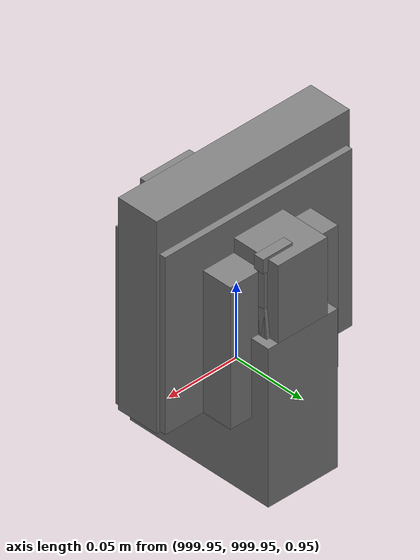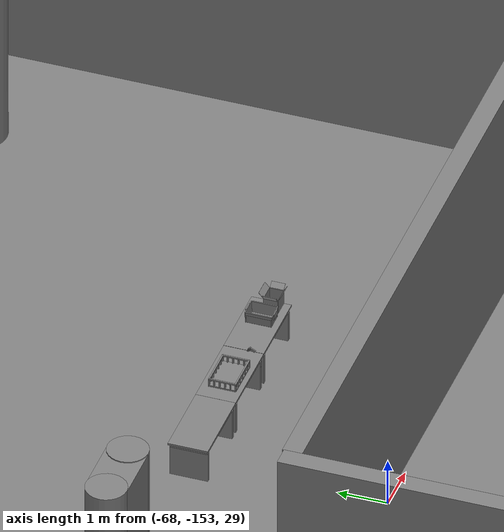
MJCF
<mujoco>
    <option gravity="0.000000000 0.000000000 -9.810000420" timestep="0.0049999999" integrator="implicitfast" density="1.225" viscosity="1.8000001e-05" noslip_iterations="10" iterations="100" sdf_iterations="50">
        <flag multiccd="disable"/>
    </option>
    <size memory="1000M"/>
    <compiler coordinate="local"/>
    <worldbody>
        <light cutoff="30" pos="0 1 1" dir="0 -1 -2"/>
        <light cutoff="30" pos="0 -1 1" dir="0 1 -2"/>
        <body pos="1000.000000000 1000.000000000 1.000000000" euler="0.000000000 0.000000000 180.000000000" name="openloong_gripper_2f85_fix_base_usda_cpu_fan">
            <geom contype="1" conaffinity="1" density="1000" type="box" material="" rgba="0.500000000 0.500000000 0.500000000 1.000000000" solimp="0.899999976 0.949999988 0.001000000" friction="1.000000000 0.005000000 0.000100000" solref="0.020000000 1.000000000" margin="0" condim="3" group="0" pos="0.000000000 0.000000000 0.070034981" quat="0.000000000 0.000000000 0.000000000 1.000000000" size="0.070700005 0.014699999 0.070700005" name="openloong_gripper_2f85_fix_base_usda_geom_4FAA2313_ACA9_4DBE_80A8_2682033F6C32"/>
            <freejoint name="openloong_gripper_2f85_fix_base_usda_cpu_fan_joint"/>
            <site size="0.005000000 0.005000000 0.005000000" rgba="0.500000000 0.500000000 0.500000000 1.000000000" pos="0.000000000 0.000000000 0.000000000" quat="0.999961913 0.008726535 0.000000000 0.000000000" group="0" type="sphere" name="openloong_gripper_2f85_fix_base_usda_cpu_fancsite"/>
        </body>
        <body pos="1000.000000000 1000.000000000 1.000000000" euler="0.000000000 0.000000000 180.000000000" name="openloong_gripper_2f85_fix_base_usda_battery_01">
            <geom contype="1" conaffinity="1" density="1000" type="box" material="" rgba="0.500000000 0.500000000 0.500000000 1.000000000" solimp="0.899999976 0.949999988 0.001000000" friction="1.000000000 0.005000000 0.000100000" solref="0.020000000 1.000000000" margin="0" condim="3" group="0" pos="-0.011123657 -0.041940309 0.101691343" quat="1.000000000 0.000000000 0.000000000 0.000000000" size="0.010800000 0.003375000 0.004725000" name="openloong_gripper_2f85_fix_base_usda_geom_AB67C5E1_1C8D_418E_B228_8EA268F7DF9F"/>
            <geom contype="1" conaffinity="1" density="1000" type="box" material="" rgba="0.500000000 0.500000000 0.500000000 1.000000000" solimp="0.899999976 0.949999988 0.001000000" friction="1.000000000 0.005000000 0.000100000" solref="0.020000000 1.000000000" margin="0" condim="3" group="0" pos="-0.010876465 -0.044247437 0.047066893" quat="0.998702705 -0.050920475 0.000000000 0.000000000" size="0.009450001 0.002700000 0.024975000" name="openloong_gripper_2f85_fix_base_usda_geom_3215F263_3E28_41B1_A26A_C4FFFEE6A112"/>
            <geom contype="1" conaffinity="1" density="1000" type="box" material="" rgba="0.500000000 0.500000000 0.500000000 1.000000000" solimp="0.899999976 0.949999988 0.001000000" friction="1.000000000 0.005000000 0.000100000" solref="0.020000000 1.000000000" margin="0" condim="3" group="0" pos="-0.001235962 -0.000659180 0.047381196" quat="1.000000000 0.000000000 0.000000000 0.000000000" size="0.039420001 0.039150000 0.047250003" name="openloong_gripper_2f85_fix_base_usda_geom_53651D62_5EE6_4EB6_9B57_EB4D5AE696E7"/>
            <geom contype="1" conaffinity="1" density="1000" type="box" material="" rgba="0.500000000 0.500000000 0.500000000 1.000000000" solimp="0.899999976 0.949999988 0.001000000" friction="1.000000000 0.005000000 0.000100000" solref="0.020000000 1.000000000" margin="0" condim="3" group="0" pos="-0.010876465 -0.039138794 0.009851727" quat="1.000000000 0.000000000 0.000000000 0.000000000" size="0.009450001 0.010800000 0.013500000" name="openloong_gripper_2f85_fix_base_usda_geom_4A920505_F01B_4593_96C9_493BC9E461DB"/>
            <geom contype="1" conaffinity="1" density="1000" type="box" material="" rgba="0.500000000 0.500000000 0.500000000 1.000000000" solimp="0.899999976 0.949999988 0.001000000" friction="1.000000000 0.005000000 0.000100000" solref="0.020000000 1.000000000" margin="0" condim="3" group="0" pos="-0.010876465 -0.041528322 0.071508206" quat="1.000000000 0.000000000 0.000000000 0.000000000" size="0.009450001 0.002700000 0.027000001" name="openloong_gripper_2f85_fix_base_usda_geom_DBE174BE_3881_48A3_8A23_5C615A8E60B7"/>
            <freejoint name="openloong_gripper_2f85_fix_base_usda_battery_01_joint"/>
            <site size="0.005000000 0.005000000 0.005000000" rgba="0.500000000 0.500000000 0.500000000 1.000000000" pos="0.000000000 0.000000000 0.000000000" quat="0.999961913 0.008726500 0.000000000 0.000000000" group="0" type="sphere" name="openloong_gripper_2f85_fix_base_usda_battery_01site"/>
        </body>
        <body pos="-65.972702026 -149.062500000 31.169099808" euler="-83.230598450 -74.342742920 -147.434219360" mocap="true" name="spotlight3_SpotLight"/>
        <body pos="1000.000000000 1000.000000000 1.000000000" euler="0.000000000 0.000000000 180.000000000" name="openloong_gripper_2f85_fix_base_usda_wifi_box">
            <geom contype="1" conaffinity="1" density="1000" type="box" material="" rgba="0.500000000 0.500000000 0.500000000 1.000000000" solimp="0.899999976 0.949999988 0.001000000" friction="1.000000000 0.005000000 0.000100000" solref="0.020000000 1.000000000" margin="0" condim="3" group="0" pos="0.000000000 0.000000000 0.058978677" quat="0.000000000 0.000000047 0.000000000 1.000000000" size="0.068499997 0.018999999 0.059000000" name="openloong_gripper_2f85_fix_base_usda_geom_BBD449F4_6677_4542_BFB6_D2BCA72F346C"/>
            <freejoint name="openloong_gripper_2f85_fix_base_usda_wifi_box_joint"/>
            <site size="0.005000000 0.005000000 0.005000000" rgba="0.500000000 0.500000000 0.500000000 1.000000000" pos="0.000000000 0.000000000 0.000000000" quat="0.999961913 0.008726500 0.000000000 0.000000000" group="0" type="sphere" name="openloong_gripper_2f85_fix_base_usda_wifi_boxsite"/>
        </body>
        <body pos="1000.000000000 1000.000000000 1.000000000" euler="0.000011953 0.000005123 -179.999984741" name="openloong_gripper_2f85_fix_base_usda_intel_box">
            <geom contype="1" conaffinity="1" density="1000" type="box" material="" rgba="0.500000000 0.500000000 0.500000000 1.000000000" solimp="0.899999976 0.949999988 0.001000000" friction="1.000000000 0.005000000 0.000100000" solref="0.020000000 1.000000000" margin="0" condim="3" group="0" pos="0.000000000 -0.000067139 0.000082284" quat="0.707106709 0.000000225 0.000000253 0.707106650" size="0.052800003 0.025300000 0.052800003" name="openloong_gripper_2f85_fix_base_usda_geom_C6BA2A71_702B_49E2_88B5_09418D375C8F"/>
            <freejoint name="openloong_gripper_2f85_fix_base_usda_intel_box_joint"/>
            <site size="0.005000000 0.005000000 0.005000000" rgba="0.500000000 0.500000000 0.500000000 1.000000000" pos="0.000000000 0.000000000 0.000000000" quat="0.999961913 0.008726500 0.000000000 0.000000000" group="0" type="sphere" name="openloong_gripper_2f85_fix_base_usda_intel_boxsite"/>
        </body>
        <body pos="-66.337951660 -149.085174561 31.171342850" euler="-56.071605682 -10.953326225 -129.862045288" mocap="true" name="spotlight5_SpotLight"/>
        <body pos="1000.000000000 999.999938965 1.000000000" euler="0.000000000 0.000000000 180.000000000" name="openloong_gripper_2f85_fix_base_usda_intelcore_i5">
            <geom contype="1" conaffinity="1" density="1000" type="box" material="" rgba="0.500000000 0.500000000 0.500000000 1.000000000" solimp="0.899999976 0.949999988 0.001000000" friction="1.000000000 0.005000000 0.000100000" solref="0.020000000 1.000000000" margin="0" condim="3" group="0" pos="0.000000000 0.000000000 0.051722717" quat="0.707106709 0.000000000 0.000000000 -0.707106769" size="0.052800000 0.018080002 0.052800000" name="openloong_gripper_2f85_fix_base_usda_geom_F30CEEF0_5F8B_4955_8824_78B25AE8E4BB"/>
            <freejoint name="openloong_gripper_2f85_fix_base_usda_intelcore_i5_joint"/>
            <site size="0.005000000 0.005000000 0.005000000" rgba="0.500000000 0.500000000 0.500000000 1.000000000" pos="0.000000000 0.000000000 0.000000000" quat="0.999961913 0.008726534 0.000000000 0.000000000" group="0" type="sphere" name="openloong_gripper_2f85_fix_base_usda_intelcore_i5site"/>
        </body>
        <body pos="-65.927902222 -149.016525269 31.165882111" euler="173.888427734 58.355411530 -42.151397705" mocap="true" name="spotlight1_SpotLight"/>
        <body pos="-64.866622925 -149.383972168 30.183746338" euler="89.999984741 89.999946594 0.000000000" name="openloong_gripper_2f85_fix_base_usda_bluebox_01">
            <geom contype="1" conaffinity="1" density="1000" type="box" material="" rgba="0.500000000 0.500000000 0.500000000 1.000000000" solimp="0.899999976 0.949999988 0.001000000" friction="1.000000000 0.005000000 0.000100000" solref="0.020000000 1.000000000" margin="0" condim="3" group="0" pos="0.276580811 0.187225342 0.000068665" quat="0.707106948 0.000077471 0.707106352 0.000077486" size="0.100000001 0.057999998 0.010000000" name="openloong_gripper_2f85_fix_base_usda_geom_99141697_C61C_4277_AB70_36E209B42CCE"/>
            <geom contype="1" conaffinity="1" density="1000" type="box" material="" rgba="0.500000000 0.500000000 0.500000000 1.000000000" solimp="0.899999976 0.949999988 0.001000000" friction="1.000000000 0.005000000 0.000100000" solref="0.020000000 1.000000000" margin="0" condim="3" group="0" pos="0.000000000 0.002883911 0.000000000" quat="0.999999881 0.000000000 0.000000000 0.000000000" size="0.254000008 0.003000000 0.172000006" name="openloong_gripper_2f85_fix_base_usda_geom_7560EFE3_3D98_4EC5_B6B2_5C27DF50ABD8"/>
            <geom contype="1" conaffinity="1" density="1000" type="box" material="" rgba="0.500000000 0.500000000 0.500000000 1.000000000" solimp="0.899999976 0.949999988 0.001000000" friction="1.000000000 0.005000000 0.000100000" solref="0.020000000 1.000000000" margin="0" condim="3" group="0" pos="0.000000000 0.124874115 0.173484802" quat="0.999796331 0.020176515 -0.000000015 0.000000030" size="0.259999990 0.119999997 0.007000000" name="openloong_gripper_2f85_fix_base_usda_geom_8633753F_F878_4AE7_9F4B_48A000AA536A"/>
            <geom contype="1" conaffinity="1" density="1000" type="box" material="" rgba="0.500000000 0.500000000 0.500000000 1.000000000" solimp="0.899999976 0.949999988 0.001000000" friction="1.000000000 0.005000000 0.000100000" solref="0.020000000 1.000000000" margin="0" condim="3" group="0" pos="0.000000000 0.124874115 -0.173469543" quat="0.999796331 -0.020176545 -0.000000015 0.000000000" size="0.259999990 0.119999997 0.007000000" name="openloong_gripper_2f85_fix_base_usda_geom_8C08788D_E3E1_4929_A96E_A36B435E130D"/>
            <geom contype="1" conaffinity="1" density="1000" type="box" material="" rgba="0.500000000 0.500000000 0.500000000 1.000000000" solimp="0.899999976 0.949999988 0.001000000" friction="1.000000000 0.005000000 0.000100000" solref="0.020000000 1.000000000" margin="0" condim="3" group="0" pos="0.000000000 0.214008331 0.188980103" quat="0.999912977 0.013176724 0.000000015 0.000000000" size="0.259999990 0.029999999 0.012500000" name="openloong_gripper_2f85_fix_base_usda_geom_F055F71D_8525_4D37_AA10_FC7AD2F919BB"/>
            <geom contype="1" conaffinity="1" density="1000" type="box" material="" rgba="0.500000000 0.500000000 0.500000000 1.000000000" solimp="0.899999976 0.949999988 0.001000000" friction="1.000000000 0.005000000 0.000100000" solref="0.020000000 1.000000000" margin="0" condim="3" group="0" pos="-0.258361816 0.125289917 0.001876831" quat="0.702796936 -0.020792112 0.710783124 0.020769298" size="0.189999998 0.119999997 0.009000000" name="openloong_gripper_2f85_fix_base_usda_geom_8272B5CF_AA6D_4315_9085_456060E4F5C1"/>
            <geom contype="1" conaffinity="1" density="1000" type="box" material="" rgba="0.500000000 0.500000000 0.500000000 1.000000000" solimp="0.899999976 0.949999988 0.001000000" friction="1.000000000 0.005000000 0.000100000" solref="0.020000000 1.000000000" margin="0" condim="3" group="0" pos="0.000000000 0.214008331 -0.188980103" quat="0.999912977 -0.013176769 0.000000030 0.000000015" size="0.259999990 0.029999999 0.012500000" name="openloong_gripper_2f85_fix_base_usda_geom_A37EAC25_EE77_404A_845A_B08AC6DC490E"/>
            <geom contype="1" conaffinity="1" density="1000" type="box" material="" rgba="0.500000000 0.500000000 0.500000000 1.000000000" solimp="0.899999976 0.949999988 0.001000000" friction="1.000000000 0.005000000 0.000100000" solref="0.020000000 1.000000000" margin="0" condim="3" group="0" pos="-0.276611328 0.187225342 0.000068665" quat="0.707106650 0.000077441 0.707106709 0.000077456" size="0.100000001 0.057999998 0.010000000" name="openloong_gripper_2f85_fix_base_usda_geom_886D0011_1C23_4B0B_A06C_FA523531123F"/>
            <geom contype="1" conaffinity="1" density="1000" type="box" material="" rgba="0.500000000 0.500000000 0.500000000 1.000000000" solimp="0.899999976 0.949999988 0.001000000" friction="1.000000000 0.005000000 0.000100000" solref="0.020000000 1.000000000" margin="0" condim="3" group="0" pos="0.258331299 0.125289917 0.001876831" quat="0.702851415 0.018856421 0.710823774 -0.019329369" size="0.189999998 0.119999997 0.009000000" name="openloong_gripper_2f85_fix_base_usda_geom_B4D9B207_9027_4020_A8C4_26484DA7DA56"/>
            <freejoint name="openloong_gripper_2f85_fix_base_usda_bluebox_01_joint"/>
            <site size="0.005000000 0.005000000 0.005000000" rgba="0.500000000 0.500000000 0.500000000 1.000000000" pos="0.000000000 0.000000000 0.000000000" quat="0.999961913 0.008726534 0.000000000 0.000000000" group="0" type="sphere" name="openloong_gripper_2f85_fix_base_usda_bluebox_01site"/>
        </body>
        <body pos="-64.496299744 -149.491867065 30.235729218" euler="0.000000000 0.000000000 89.999946594" name="openloong_gripper_2f85_fix_base_usda_cardboardbox_01">
            <geom contype="1" conaffinity="1" density="1000" type="box" material="" rgba="0.500000000 0.500000000 0.500000000 1.000000000" solimp="0.899999976 0.949999988 0.001000000" friction="1.000000000 0.005000000 0.000100000" solref="0.020000000 1.000000000" margin="0" condim="3" group="0" pos="-0.003166199 -0.004086494 0.005052090" quat="1.000000000 0.000000000 0.000000000 0.000000000" size="0.142499998 0.177500010 0.005000000" name="openloong_gripper_2f85_fix_base_usda_geom_742724C6_A21D_40F8_90D8_C9577B946F5C"/>
            <geom contype="1" conaffinity="1" density="1000" type="box" material="" rgba="0.500000000 0.500000000 0.500000000 1.000000000" solimp="0.899999976 0.949999988 0.001000000" friction="1.000000000 0.005000000 0.000100000" solref="0.020000000 1.000000000" margin="0" condim="3" group="0" pos="-0.003166199 0.170316696 0.150570869" quat="1.000000000 0.000000000 0.000000000 0.000000000" size="0.142499998 0.005000000 0.149999991" name="openloong_gripper_2f85_fix_base_usda_geom_A9CECDE7_D52B_45D1_BCCA_C93BA3014679"/>
            <geom contype="1" conaffinity="1" density="1000" type="box" material="" rgba="0.500000000 0.500000000 0.500000000 1.000000000" solimp="0.899999976 0.949999988 0.001000000" friction="1.000000000 0.005000000 0.000100000" solref="0.020000000 1.000000000" margin="0" condim="3" group="0" pos="-0.147399902 -0.005307198 0.150570869" quat="1.000000000 0.000000000 0.000000000 0.000000000" size="0.005000000 0.177500010 0.149999991" name="openloong_gripper_2f85_fix_base_usda_geom_2FD2BB85_CCF4_40E7_A199_4758D1400916"/>
            <geom contype="1" conaffinity="1" density="1000" type="box" material="" rgba="0.500000000 0.500000000 0.500000000 1.000000000" solimp="0.899999976 0.949999988 0.001000000" friction="1.000000000 0.005000000 0.000100000" solref="0.020000000 1.000000000" margin="0" condim="3" group="0" pos="0.140275955 -0.005307198 0.150570869" quat="1.000000000 0.000000000 0.000000000 0.000000000" size="0.005000000 0.177500010 0.149999991" name="openloong_gripper_2f85_fix_base_usda_geom_AD0DB46C_608D_4F09_9AA3_589204D7796A"/>
            <geom contype="1" conaffinity="1" density="1000" type="box" material="" rgba="0.500000000 0.500000000 0.500000000 1.000000000" solimp="0.899999976 0.949999988 0.001000000" friction="1.000000000 0.005000000 0.000100000" solref="0.020000000 1.000000000" margin="0" condim="3" group="0" pos="-0.003166199 -0.181550980 0.150570869" quat="1.000000000 0.000000000 0.000000000 0.000000000" size="0.142499998 0.005000000 0.149999991" name="openloong_gripper_2f85_fix_base_usda_geom_20DB7A05_693F_4D0F_A8E4_F46D92036F23"/>
            <freejoint name="openloong_gripper_2f85_fix_base_usda_cardboardbox_01_joint"/>
            <site size="0.005000000 0.005000000 0.005000000" rgba="0.500000000 0.500000000 0.500000000 1.000000000" pos="0.000000000 0.000000000 0.000000000" quat="0.999961913 0.008726535 0.000000000 0.000000000" group="0" type="sphere" name="openloong_gripper_2f85_fix_base_usda_site_229F6A13_9010_44D0_A7EE_0CC31698B0EE"/>
            <body pos="0.139160156 -0.004048347 0.301930904" euler="-179.999954224 49.383502960 179.999954224" name="openloong_gripper_2f85_fix_base_usda_A1_006">
                <geom contype="1" conaffinity="1" density="1000" type="box" material="" rgba="0.500000000 0.500000000 0.500000000 1.000000000" solimp="0.899999976 0.949999988 0.001000000" friction="1.000000000 0.005000000 0.000100000" solref="0.020000000 1.000000000" margin="0" condim="3" group="0" pos="-0.071587563 0.000009537 0.001745224" quat="0.999999881 0.000000000 0.000000000 0.000000000" size="0.071249999 0.179999992 0.002500000" name="openloong_gripper_2f85_fix_base_usda_geom_7725E12B_55CE_48EB_9AC3_32BD447323FF"/>
                <joint armature="0" stiffness="0.07" damping="0.0099999998" axis="0.000000 1.000000 0.000000" type="hinge" name="openloong_gripper_2f85_fix_base_usda_A1_006"/>
            </body>
            <body pos="-0.145902634 -0.004086494 0.301938057" euler="-180.000000000 -60.000011444 -180.000000000" name="openloong_gripper_2f85_fix_base_usda_A2_006">
                <geom contype="1" conaffinity="1" density="1000" type="box" material="" rgba="0.500000000 0.500000000 0.500000000 1.000000000" solimp="0.899999976 0.949999988 0.001000000" friction="1.000000000 0.005000000 0.000100000" solref="0.020000000 1.000000000" margin="0" condim="3" group="0" pos="0.071268082 0.000009537 0.002717972" quat="0.000002921 0.000000000 -0.000000030 0.999999881" size="0.071249999 0.179999992 0.002500000" name="openloong_gripper_2f85_fix_base_usda_geom_BF9CD66D_5696_4F35_B11F_CE6DCCFF6FE0"/>
                <joint armature="0" stiffness="0.07" damping="0.0099999998" axis="0.000000 1.000000 0.000000" type="hinge" name="openloong_gripper_2f85_fix_base_usda_A2_006"/>
            </body>
            <body pos="-0.003385544 0.175991058 0.301930904" euler="-125.858116150 -0.000004561 0.000002331" name="openloong_gripper_2f85_fix_base_usda_B2_006">
                <geom contype="1" conaffinity="1" density="1000" type="box" material="" rgba="0.500000000 0.500000000 0.500000000 1.000000000" solimp="0.899999976 0.949999988 0.001000000" friction="1.000000000 0.005000000 0.000100000" solref="0.020000000 1.000000000" margin="0" condim="3" group="0" pos="0.000009537 -0.070939064 -0.002470016" quat="0.999614120 0.027776197 -0.000000015 0.000000030" size="0.137500003 0.064999998 0.005000000" name="openloong_gripper_2f85_fix_base_usda_geom_E2FDA9B1_FC7E_4310_B551_D263135FEAF9"/>
                <joint armature="0" stiffness="0.07" damping="0.0099999998" axis="1.000000 0.000000 0.000000" type="hinge" name="openloong_gripper_2f85_fix_base_usda_B2_006"/>
            </body>
            <body pos="-0.003385544 -0.184140205 0.301938057" euler="147.805557251 0.000000000 0.000000000" name="openloong_gripper_2f85_fix_base_usda_B1_006">
                <geom contype="1" conaffinity="1" density="1000" type="box" material="" rgba="0.500000000 0.500000000 0.500000000 1.000000000" solimp="0.899999976 0.949999988 0.001000000" friction="1.000000000 0.005000000 0.000100000" solref="0.020000000 1.000000000" margin="0" condim="3" group="0" pos="-0.000028610 0.070202351 -0.002703667" quat="0.999614179 -0.027776167 0.000000000 0.000000000" size="0.137500003 0.064999998 0.005000000" name="openloong_gripper_2f85_fix_base_usda_geom_B16B7EA1_1D47_4D59_96C1_B8E682C73CB5"/>
                <joint armature="0" stiffness="0.07" damping="0.0099999998" axis="1.000000 0.000000 0.000000" type="hinge" name="openloong_gripper_2f85_fix_base_usda_B1_006"/>
            </body>
        </body>
        <body pos="-65.882858276 -149.481979370 30.229999542" euler="-64.487716675 0.000000000 0.000000000" name="openloong_gripper_2f85_fix_base_usda_Barcode">
            <geom contype="1" conaffinity="1" density="1000" type="box" material="" rgba="0.500000000 0.500000000 0.500000000 1.000000000" solimp="0.899999976 0.949999988 0.001000000" friction="1.000000000 0.005000000 0.000100000" solref="0.020000000 1.000000000" margin="0" condim="3" group="0" pos="0.000000000 0.013038635 0.001419067" quat="0.000000000 0.000000000 0.000000000 1.000000119" size="0.034000002 0.010000000 0.017999999" name="openloong_gripper_2f85_fix_base_usda_geom_5E76E80F_76A9_44FC_8EFA_824111C88C58"/>
            <geom contype="1" conaffinity="1" density="1000" type="box" material="" rgba="0.500000000 0.500000000 0.500000000 1.000000000" solimp="0.899999976 0.949999988 0.001000000" friction="1.000000000 0.005000000 0.000100000" solref="0.020000000 1.000000000" margin="0" condim="3" group="0" pos="0.000000000 -0.035301208 -0.007095337" quat="0.000000000 0.000000000 -0.043619365 0.999048233" size="0.028999999 0.010000000 0.020000000" name="openloong_gripper_2f85_fix_base_usda_geom_9E4DF57C_97A2_4591_90DD_7AD91C9DC5D3"/>
            <geom contype="1" conaffinity="1" density="1000" type="box" material="" rgba="0.500000000 0.500000000 0.500000000 1.000000000" solimp="0.899999976 0.949999988 0.001000000" friction="1.000000000 0.005000000 0.000100000" solref="0.020000000 1.000000000" margin="0" condim="3" group="0" pos="0.000000000 -0.043411255 -0.011749268" quat="0.922262907 0.386563420 0.000000000 0.000000000" size="0.026000001 0.010000000 0.020000000" name="openloong_gripper_2f85_fix_base_usda_geom_7341A06B_E757_4C23_9FC8_A619F5FEEA69"/>
            <geom contype="1" conaffinity="1" density="1000" type="box" material="" rgba="0.500000000 0.500000000 0.500000000 1.000000000" solimp="0.899999976 0.949999988 0.001000000" friction="1.000000000 0.005000000 0.000100000" solref="0.020000000 1.000000000" margin="0" condim="3" group="0" pos="0.000000000 -0.016967773 -0.031860352" quat="0.000000000 0.000000000 0.000000000 1.000000119" size="0.008000000 0.010000000 0.013000000" name="openloong_gripper_2f85_fix_base_usda_geom_A43CBC6E_C98E_46C4_870D_8415D7798E24"/>
            <geom contype="1" conaffinity="1" density="1000" type="box" material="" rgba="0.500000000 0.500000000 0.500000000 1.000000000" solimp="0.899999976 0.949999988 0.001000000" friction="1.000000000 0.005000000 0.000100000" solref="0.020000000 1.000000000" margin="0" condim="3" group="0" pos="0.000000000 -0.001869202 0.000312805" quat="0.953716993 0.300705761 0.000000000 0.000000000" size="0.032000002 0.010000000 0.018999999" name="openloong_gripper_2f85_fix_base_usda_geom_90492387_7F30_42D6_8303_8FCB5EE71CE2"/>
            <geom contype="1" conaffinity="1" density="1000" type="box" material="" rgba="0.500000000 0.500000000 0.500000000 1.000000000" solimp="0.899999976 0.949999988 0.001000000" friction="1.000000000 0.005000000 0.000100000" solref="0.020000000 1.000000000" margin="0" condim="3" group="0" pos="0.000000000 -0.019531250 -0.003173828" quat="0.953716993 0.300705761 0.000000000 0.000000000" size="0.030999999 0.010000000 0.020000000" name="openloong_gripper_2f85_fix_base_usda_geom_32FD22F8_C698_4E23_8863_9E9B180D3014"/>
            <geom contype="1" conaffinity="1" density="1000" type="box" material="" rgba="0.500000000 0.500000000 0.500000000 1.000000000" solimp="0.899999976 0.949999988 0.001000000" friction="1.000000000 0.005000000 0.000100000" solref="0.020000000 1.000000000" margin="0" condim="3" group="0" pos="0.000000000 -0.035301208 -0.007095337" quat="0.953716993 0.300705761 0.000000000 0.000000000" size="0.028999999 0.010000000 0.020000000" name="openloong_gripper_2f85_fix_base_usda_geom_A2D7F1D6_5A6D_4A2A_928B_1A1CEC3C18BA"/>
            <geom contype="1" conaffinity="1" density="1000" type="box" material="" rgba="0.500000000 0.500000000 0.500000000 1.000000000" solimp="0.899999976 0.949999988 0.001000000" friction="1.000000000 0.005000000 0.000100000" solref="0.020000000 1.000000000" margin="0" condim="3" group="0" pos="0.000000000 -0.042617798 -0.071121216" quat="0.000000000 0.000000000 0.000000000 1.000000119" size="0.013000000 0.021000000 0.059999999" name="openloong_gripper_2f85_fix_base_usda_geom_BB69FC17_7CBF_4BE6_8A32_8327D0B58EC2"/>
            <freejoint name="openloong_gripper_2f85_fix_base_usda_Barcode_joint"/>
            <site size="0.005000000 0.005000000 0.005000000" rgba="0.500000000 0.500000000 0.500000000 1.000000000" pos="0.000000000 0.000000000 0.000000000" quat="1.000000000 0.000000000 0.000000000 0.000000000" group="0" type="sphere" name="openloong_gripper_2f85_fix_base_usda_Barcode_site"/>
        </body>
        <body pos="-66.745018005 -149.392349243 30.184000015" euler="0.000000000 0.000000000 89.999946594" name="[22332087835077]_Basket_01">
            <geom contype="1" conaffinity="1" density="1000" type="box" material="" rgba="0.500000000 0.500000000 0.500000000 1.000000000" solimp="0.899999976 0.949999988 0.001000000" friction="1.000000000 0.005000000 0.000100000" solref="0.020000000 1.000000000" margin="0" condim="3" group="0" pos="-0.052425385 0.389207840 0.089787483" quat="0.707107008 0.000000000 0.000000000 0.707106411" size="0.014249999 0.014249999 0.059999999" name="[22332087835077]_geom_72135CB4_F70E_44C6_BE61_DF6A75175532"/>
            <geom contype="1" conaffinity="1" density="1000" type="box" material="" rgba="0.500000000 0.500000000 0.500000000 1.000000000" solimp="0.899999976 0.949999988 0.001000000" friction="1.000000000 0.005000000 0.000100000" solref="0.020000000 1.000000000" margin="0" condim="3" group="0" pos="0.264015198 -0.133043289 0.089787483" quat="0.707107008 0.000000000 0.000000000 0.707106411" size="0.014249999 0.014249999 0.059999999" name="[22332087835077]_geom_C26025DE_B189_4C93_B19B_5B1B03CEC265"/>
            <geom contype="1" conaffinity="1" density="1000" type="box" material="" rgba="0.500000000 0.500000000 0.500000000 1.000000000" solimp="0.899999976 0.949999988 0.001000000" friction="1.000000000 0.005000000 0.000100000" solref="0.020000000 1.000000000" margin="0" condim="3" group="0" pos="-0.264015198 -0.265548706 0.089793205" quat="0.707107008 0.000000000 0.000000000 0.707106411" size="0.014249999 0.014249999 0.059999999" name="[22332087835077]_geom_02B539E2_F96A_40CA_8E7E_4BEB1A558EF3"/>
            <geom contype="1" conaffinity="1" density="1000" type="box" material="" rgba="0.500000000 0.500000000 0.500000000 1.000000000" solimp="0.899999976 0.949999988 0.001000000" friction="1.000000000 0.005000000 0.000100000" solref="0.020000000 1.000000000" margin="0" condim="3" group="0" pos="-0.160263062 -0.389322281 0.089793205" quat="0.707107008 0.000000000 0.000000000 0.707106411" size="0.014249999 0.014249999 0.059999999" name="[22332087835077]_geom_103311FC_FC31_43A2_ABD3_64804BC8E632"/>
            <geom contype="1" conaffinity="1" density="1000" type="box" material="" rgba="0.500000000 0.500000000 0.500000000 1.000000000" solimp="0.899999976 0.949999988 0.001000000" friction="1.000000000 0.005000000 0.000100000" solref="0.020000000 1.000000000" margin="0" condim="3" group="0" pos="0.162265778 -0.389322281 0.089787483" quat="0.707107008 0.000000000 0.000000000 0.707106411" size="0.014249999 0.014249999 0.059999999" name="[22332087835077]_geom_A19CCBBF_C86C_4905_91CA_4DA9823D81F4"/>
            <geom contype="1" conaffinity="1" density="1000" type="box" material="" rgba="0.500000000 0.500000000 0.500000000 1.000000000" solimp="0.899999976 0.949999988 0.001000000" friction="1.000000000 0.005000000 0.000100000" solref="0.020000000 1.000000000" margin="0" condim="3" group="0" pos="0.264015198 0.389207840 0.089787483" quat="0.707107008 0.000000000 0.000000000 0.707106411" size="0.014249999 0.014249999 0.059999999" name="[22332087835077]_geom_46CD4B91_6133_4E90_9E0D_12E23E822877"/>
            <geom contype="1" conaffinity="1" density="1000" type="box" material="" rgba="0.500000000 0.500000000 0.500000000 1.000000000" solimp="0.899999976 0.949999988 0.001000000" friction="1.000000000 0.005000000 0.000100000" solref="0.020000000 1.000000000" margin="0" condim="3" group="0" pos="-0.264015198 -0.133043289 0.089793205" quat="0.707107008 0.000000000 0.000000000 0.707106411" size="0.014249999 0.014249999 0.059999999" name="[22332087835077]_geom_60241E48_4811_4D04_862C_031CF6DFB877"/>
            <geom contype="1" conaffinity="1" density="1000" type="box" material="" rgba="0.500000000 0.500000000 0.500000000 1.000000000" solimp="0.899999976 0.949999988 0.001000000" friction="1.000000000 0.005000000 0.000100000" solref="0.020000000 1.000000000" margin="0" condim="3" group="0" pos="-0.264026642 0.269256592 0.089793205" quat="0.707107008 0.000000000 0.000000000 0.707106411" size="0.014249999 0.014249999 0.059999999" name="[22332087835077]_geom_A745B39E_1E4F_4D76_9321_86088BB405C4"/>
            <geom contype="1" conaffinity="1" density="1000" type="box" material="" rgba="0.500000000 0.500000000 0.500000000 1.000000000" solimp="0.899999976 0.949999988 0.001000000" friction="1.000000000 0.005000000 0.000100000" solref="0.020000000 1.000000000" margin="0" condim="3" group="0" pos="0.054462433 0.389207840 0.089787483" quat="0.707107008 0.000000000 0.000000000 0.707106411" size="0.014249999 0.014249999 0.059999999" name="[22332087835077]_geom_CC288C1C_6D40_4178_A69B_7F45BD5FB00B"/>
            <geom contype="1" conaffinity="1" density="1000" type="box" material="" rgba="0.500000000 0.500000000 0.500000000 1.000000000" solimp="0.899999976 0.949999988 0.001000000" friction="1.000000000 0.005000000 0.000100000" solref="0.020000000 1.000000000" margin="0" condim="3" group="0" pos="0.054462433 -0.389322281 0.089787483" quat="0.707107008 0.000000000 0.000000000 0.707106411" size="0.014249999 0.014249999 0.059999999" name="[22332087835077]_geom_474A6ED5_61D0_4B8E_9836_939095786E85"/>
            <geom contype="1" conaffinity="1" density="1000" type="box" material="" rgba="0.500000000 0.500000000 0.500000000 1.000000000" solimp="0.899999976 0.949999988 0.001000000" friction="1.000000000 0.005000000 0.000100000" solref="0.020000000 1.000000000" margin="0" condim="3" group="0" pos="0.264015198 0.269256592 0.089793205" quat="0.707107008 0.000000000 0.000000000 0.707106411" size="0.014249999 0.014249999 0.059999999" name="[22332087835077]_geom_CFA75E95_5098_4AF8_BB92_281B7B0F7A91"/>
            <geom contype="1" conaffinity="1" density="1000" type="box" material="" rgba="0.500000000 0.500000000 0.500000000 1.000000000" solimp="0.899999976 0.949999988 0.001000000" friction="1.000000000 0.005000000 0.000100000" solref="0.020000000 1.000000000" margin="0" condim="3" group="0" pos="0.264015198 -0.389322281 0.089787483" quat="0.707107008 0.000000000 0.000000000 0.707106411" size="0.014249999 0.014249999 0.059999999" name="[22332087835077]_geom_22908A75_4B01_49C8_9334_F21EBF09F9B4"/>
            <geom contype="1" conaffinity="1" density="1000" type="box" material="" rgba="0.500000000 0.500000000 0.500000000 1.000000000" solimp="0.899999976 0.949999988 0.001000000" friction="1.000000000 0.005000000 0.000100000" solref="0.020000000 1.000000000" margin="0" condim="3" group="0" pos="0.000000000 0.000000000 0.015998840" quat="0.707107008 0.000000000 0.000000000 0.707106411" size="0.403499991 0.279000014 0.015750000" name="[22332087835077]_geom_289EEB16_9155_49B5_9BD4_3158DDA7E4A3"/>
            <geom contype="1" conaffinity="1" density="1000" type="box" material="" rgba="0.500000000 0.500000000 0.500000000 1.000000000" solimp="0.899999976 0.949999988 0.001000000" friction="1.000000000 0.005000000 0.000100000" solref="0.020000000 1.000000000" margin="0" condim="3" group="0" pos="0.000000000 -0.389476776 0.163619041" quat="0.707107008 0.000000000 0.000000000 0.707106411" size="0.015000000 0.277500004 0.015750000" name="[22332087835077]_geom_DB337DA1_3B07_49FA_ADA4_70B409848E4D"/>
            <geom contype="1" conaffinity="1" density="1000" type="box" material="" rgba="0.500000000 0.500000000 0.500000000 1.000000000" solimp="0.899999976 0.949999988 0.001000000" friction="1.000000000 0.005000000 0.000100000" solref="0.020000000 1.000000000" margin="0" condim="3" group="0" pos="0.162265778 0.389207840 0.089787483" quat="0.707107008 0.000000000 0.000000000 0.707106411" size="0.014249999 0.014249999 0.059999999" name="[22332087835077]_geom_97E544A5_B77E_4BB3_9EDF_3340EC04F1AB"/>
            <geom contype="1" conaffinity="1" density="1000" type="box" material="" rgba="0.500000000 0.500000000 0.500000000 1.000000000" solimp="0.899999976 0.949999988 0.001000000" friction="1.000000000 0.005000000 0.000100000" solref="0.020000000 1.000000000" margin="0" condim="3" group="0" pos="0.000000000 0.389471054 0.163619041" quat="0.707107008 0.000000000 0.000000000 0.707106411" size="0.015000000 0.277500004 0.015750000" name="[22332087835077]_geom_A9C7BF7F_C13B_4EB2_83D1_746539897D4F"/>
            <geom contype="1" conaffinity="1" density="1000" type="box" material="" rgba="0.500000000 0.500000000 0.500000000 1.000000000" solimp="0.899999976 0.949999988 0.001000000" friction="1.000000000 0.005000000 0.000100000" solref="0.020000000 1.000000000" margin="0" condim="3" group="0" pos="-0.263511658 0.000000000 0.163619041" quat="0.707107008 0.000000000 0.000000000 0.707106411" size="0.403499991 0.015000000 0.015750000" name="[22332087835077]_geom_47D946F5_20ED_4800_9760_9474FDB6940D"/>
            <geom contype="1" conaffinity="1" density="1000" type="box" material="" rgba="0.500000000 0.500000000 0.500000000 1.000000000" solimp="0.899999976 0.949999988 0.001000000" friction="1.000000000 0.005000000 0.000100000" solref="0.020000000 1.000000000" margin="0" condim="3" group="0" pos="-0.264015198 0.141334534 0.089793205" quat="0.707107008 0.000000000 0.000000000 0.707106411" size="0.014249999 0.014249999 0.059999999" name="[22332087835077]_geom_F8B37004_DAC7_4DBB_9152_E0660E31AFE2"/>
            <geom contype="1" conaffinity="1" density="1000" type="box" material="" rgba="0.500000000 0.500000000 0.500000000 1.000000000" solimp="0.899999976 0.949999988 0.001000000" friction="1.000000000 0.005000000 0.000100000" solref="0.020000000 1.000000000" margin="0" condim="3" group="0" pos="0.264015198 -0.265548706 0.089787483" quat="0.707107008 0.000000000 0.000000000 0.707106411" size="0.014249999 0.014249999 0.059999999" name="[22332087835077]_geom_235C2AF8_FCB7_437E_A7B2_2960B2586E44"/>
            <geom contype="1" conaffinity="1" density="1000" type="box" material="" rgba="0.500000000 0.500000000 0.500000000 1.000000000" solimp="0.899999976 0.949999988 0.001000000" friction="1.000000000 0.005000000 0.000100000" solref="0.020000000 1.000000000" margin="0" condim="3" group="0" pos="-0.160263062 0.389207840 0.089787483" quat="0.707107008 0.000000000 0.000000000 0.707106411" size="0.014249999 0.014249999 0.059999999" name="[22332087835077]_geom_F1834F09_A8FC_47A8_8C03_AB42F0BD2C73"/>
            <geom contype="1" conaffinity="1" density="1000" type="box" material="" rgba="0.500000000 0.500000000 0.500000000 1.000000000" solimp="0.899999976 0.949999988 0.001000000" friction="1.000000000 0.005000000 0.000100000" solref="0.020000000 1.000000000" margin="0" condim="3" group="0" pos="-0.052425385 -0.389322281 0.089787483" quat="0.707107008 0.000000000 0.000000000 0.707106411" size="0.014249999 0.014249999 0.059999999" name="[22332087835077]_geom_FFFD44C4_81C0_4ED2_90FD_F0B9A6AB93F2"/>
            <geom contype="1" conaffinity="1" density="1000" type="box" material="" rgba="0.500000000 0.500000000 0.500000000 1.000000000" solimp="0.899999976 0.949999988 0.001000000" friction="1.000000000 0.005000000 0.000100000" solref="0.020000000 1.000000000" margin="0" condim="3" group="0" pos="-0.264026642 -0.389322281 0.089793205" quat="0.707107008 0.000000000 0.000000000 0.707106411" size="0.014249999 0.014249999 0.059999999" name="[22332087835077]_geom_9D67BFE6_8597_4D68_AA21_27E6F0B06A08"/>
            <geom contype="1" conaffinity="1" density="1000" type="box" material="" rgba="0.500000000 0.500000000 0.500000000 1.000000000" solimp="0.899999976 0.949999988 0.001000000" friction="1.000000000 0.005000000 0.000100000" solref="0.020000000 1.000000000" margin="0" condim="3" group="0" pos="0.264015198 0.141334534 0.089787483" quat="0.707107008 0.000000000 0.000000000 0.707106411" size="0.014249999 0.014249999 0.059999999" name="[22332087835077]_geom_BC65C084_2E7B_4AC1_AFE8_04DFB0D9D39F"/>
            <geom contype="1" conaffinity="1" density="1000" type="box" material="" rgba="0.500000000 0.500000000 0.500000000 1.000000000" solimp="0.899999976 0.949999988 0.001000000" friction="1.000000000 0.005000000 0.000100000" solref="0.020000000 1.000000000" margin="0" condim="3" group="0" pos="-0.264015198 0.389207840 0.089793205" quat="0.707107008 0.000000000 0.000000000 0.707106411" size="0.014249999 0.014249999 0.059999999" name="[22332087835077]_geom_E6635136_CC0C_4664_8552_8EADF225D94E"/>
            <geom contype="1" conaffinity="1" density="1000" type="box" material="" rgba="0.500000000 0.500000000 0.500000000 1.000000000" solimp="0.899999976 0.949999988 0.001000000" friction="1.000000000 0.005000000 0.000100000" solref="0.020000000 1.000000000" margin="0" condim="3" group="0" pos="0.264015198 0.004480362 0.089787483" quat="0.707107008 0.000000000 0.000000000 0.707106411" size="0.014249999 0.014249999 0.059999999" name="[22332087835077]_geom_94D8A59F_12CA_4623_B0F5_B0625E564028"/>
            <geom contype="1" conaffinity="1" density="1000" type="box" material="" rgba="0.500000000 0.500000000 0.500000000 1.000000000" solimp="0.899999976 0.949999988 0.001000000" friction="1.000000000 0.005000000 0.000100000" solref="0.020000000 1.000000000" margin="0" condim="3" group="0" pos="0.263694763 -0.000011444 0.163619041" quat="0.707107008 0.000000000 0.000000000 0.707106411" size="0.403499991 0.015000000 0.015750000" name="[22332087835077]_geom_5A31EB20_7C8C_484D_A134_05CE0165E5A9"/>
            <geom contype="1" conaffinity="1" density="1000" type="box" material="" rgba="0.500000000 0.500000000 0.500000000 1.000000000" solimp="0.899999976 0.949999988 0.001000000" friction="1.000000000 0.005000000 0.000100000" solref="0.020000000 1.000000000" margin="0" condim="3" group="0" pos="-0.264015198 0.004480362 0.089793205" quat="0.707107008 0.000000000 0.000000000 0.707106411" size="0.014249999 0.014249999 0.059999999" name="[22332087835077]_geom_09A21A6D_E203_4258_A638_C683B14B6C86"/>
            <freejoint name="[22332087835077]_joint_E25F6852_7035_46D1_B5F3_6207B475C15A"/>
        </body>
        <body pos="0.000000000 0.000000000 0.000000000" euler="0.000000000 0.000000000 0.000000000" name="Static Objects_Static Objects">
            <geom contype="1" conaffinity="1" density="1000" type="box" material="" rgba="0.500000000 0.500000000 0.500000000 1.000000000" solimp="0.899999976 0.949999988 0.001000000" friction="1.000000000 0.005000000 0.000100000" solref="0.020000000 1.000000000" margin="0" condim="3" group="0" pos="-67.544113159 -149.365814209 29.727830887" quat="0.500000417 0.499999970 0.499999553 0.499999970" size="0.381000012 0.319999993 0.041000001" name="Static Objects_geom_9A4C8AD7_136F_4DE7_8214_A4677DE2F405"/>
            <geom contype="1" conaffinity="1" density="1000" type="box" material="" rgba="0.500000000 0.500000000 0.500000000 1.000000000" solimp="0.899999976 0.949999988 0.001000000" friction="1.000000000 0.005000000 0.000100000" solref="0.020000000 1.000000000" margin="0" condim="3" group="0" pos="-68.239501953 -149.365814209 30.086868286" quat="0.500000417 0.499999970 0.499999553 0.499999970" size="0.370999992 0.039500002 0.745000005" name="Static Objects_geom_200D4EAF_F2D2_4A6F_9B08_DFCBEE78FB50"/>
            <geom contype="1" conaffinity="1" density="1000" type="box" material="" rgba="0.500000000 0.500000000 0.500000000 1.000000000" solimp="0.899999976 0.949999988 0.001000000" friction="1.000000000 0.005000000 0.000100000" solref="0.020000000 1.000000000" margin="0" condim="3" group="0" pos="-68.239501953 -149.365814209 30.147235870" quat="0.500000417 0.499999970 0.499999553 0.499999970" size="0.400000006 0.022000000 0.800000012" name="Static Objects_geom_C5187880_A304_43E0_9C79_E85CC3AB5A03"/>
            <geom contype="1" conaffinity="1" density="1000" type="box" material="" rgba="0.500000000 0.500000000 0.500000000 1.000000000" solimp="0.899999976 0.949999988 0.001000000" friction="1.000000000 0.005000000 0.000100000" solref="0.020000000 1.000000000" margin="0" condim="3" group="0" pos="-68.934890747 -149.365814209 29.727830887" quat="0.500000417 0.499999970 0.499999553 0.499999970" size="0.381000012 0.319999993 0.041000001" name="Static Objects_geom_B90BBEB1_DAE5_4354_B8B3_739DC779C20D"/>
            <geom contype="1" conaffinity="1" density="1000" type="box" material="" rgba="0.500000000 0.500000000 0.500000000 1.000000000" solimp="0.899999976 0.949999988 0.001000000" friction="1.000000000 0.005000000 0.000100000" solref="0.020000000 1.000000000" margin="0" condim="3" group="0" pos="-68.239501953 -149.365814209 29.561563492" quat="0.500000417 0.499999970 0.499999553 0.499999970" size="0.020000000 0.022000000 0.660000026" name="Static Objects_geom_9C599B31_5ADE_442C_A196_A567985A82A1"/>
            <geom contype="1" conaffinity="1" density="1000" type="box" material="" rgba="0.500000000 0.500000000 0.500000000 1.000000000" solimp="0.899999976 0.949999988 0.001000000" friction="1.000000000 0.005000000 0.000100000" solref="0.020000000 1.000000000" margin="0" condim="3" group="0" pos="-65.945671082 -149.365814209 29.727830887" quat="0.500000417 0.499999970 0.499999553 0.499999970" size="0.381000012 0.319999993 0.041000001" name="Static Objects_geom_2A708480_0B02_48C2_9E5C_4540E514F1E3"/>
            <geom contype="1" conaffinity="1" density="1000" type="box" material="" rgba="0.500000000 0.500000000 0.500000000 1.000000000" solimp="0.899999976 0.949999988 0.001000000" friction="1.000000000 0.005000000 0.000100000" solref="0.020000000 1.000000000" margin="0" condim="3" group="0" pos="-66.641059875 -149.365814209 30.086868286" quat="0.500000417 0.499999970 0.499999553 0.499999970" size="0.370999992 0.039500002 0.745000005" name="Static Objects_geom_3EE0BA4A_DE8B_4874_BD6A_4E5621371346"/>
            <geom contype="1" conaffinity="1" density="1000" type="box" material="" rgba="0.500000000 0.500000000 0.500000000 1.000000000" solimp="0.899999976 0.949999988 0.001000000" friction="1.000000000 0.005000000 0.000100000" solref="0.020000000 1.000000000" margin="0" condim="3" group="0" pos="-66.641059875 -149.365814209 30.147235870" quat="0.500000417 0.499999970 0.499999553 0.499999970" size="0.400000006 0.022000000 0.800000012" name="Static Objects_geom_7649F251_8D96_4A83_888A_51FF738A13C0"/>
            <geom contype="1" conaffinity="1" density="1000" type="box" material="" rgba="0.500000000 0.500000000 0.500000000 1.000000000" solimp="0.899999976 0.949999988 0.001000000" friction="1.000000000 0.005000000 0.000100000" solref="0.020000000 1.000000000" margin="0" condim="3" group="0" pos="-67.336448669 -149.365814209 29.727830887" quat="0.500000417 0.499999970 0.499999553 0.499999970" size="0.381000012 0.319999993 0.041000001" name="Static Objects_geom_30775948_38CD_45F3_8170_E2E4276CB76C"/>
            <geom contype="1" conaffinity="1" density="1000" type="box" material="" rgba="0.500000000 0.500000000 0.500000000 1.000000000" solimp="0.899999976 0.949999988 0.001000000" friction="1.000000000 0.005000000 0.000100000" solref="0.020000000 1.000000000" margin="0" condim="3" group="0" pos="-66.641059875 -149.365814209 29.561563492" quat="0.500000417 0.499999970 0.499999553 0.499999970" size="0.020000000 0.022000000 0.660000026" name="Static Objects_geom_710AC1CF_D638_4C8F_8A55_D0C9EA3B5EE3"/>
            <geom contype="1" conaffinity="1" density="1000" type="box" material="" rgba="0.500000000 0.500000000 0.500000000 1.000000000" solimp="0.899999976 0.949999988 0.001000000" friction="1.000000000 0.005000000 0.000100000" solref="0.020000000 1.000000000" margin="0" condim="3" group="0" pos="-64.338577271 -149.365814209 29.727830887" quat="0.500000417 0.499999970 0.499999553 0.499999970" size="0.381000012 0.319999993 0.041000001" name="Static Objects_geom_4A2202AF_DAA4_4285_AA16_E21C00AD5280"/>
            <geom contype="1" conaffinity="1" density="1000" type="box" material="" rgba="0.500000000 0.500000000 0.500000000 1.000000000" solimp="0.899999976 0.949999988 0.001000000" friction="1.000000000 0.005000000 0.000100000" solref="0.020000000 1.000000000" margin="0" condim="3" group="0" pos="-65.033966064 -149.365814209 30.086868286" quat="0.500000417 0.499999970 0.499999553 0.499999970" size="0.370999992 0.039500002 0.745000005" name="Static Objects_geom_ABD08C89_3783_483E_9715_ADC7076D4896"/>
            <geom contype="1" conaffinity="1" density="1000" type="box" material="" rgba="0.500000000 0.500000000 0.500000000 1.000000000" solimp="0.899999976 0.949999988 0.001000000" friction="1.000000000 0.005000000 0.000100000" solref="0.020000000 1.000000000" margin="0" condim="3" group="0" pos="-65.033966064 -149.365814209 30.147235870" quat="0.500000417 0.499999970 0.499999553 0.499999970" size="0.400000006 0.022000000 0.800000012" name="Static Objects_geom_B37FE099_4E4F_4915_B8B4_3D618EFABBFD"/>
            <geom contype="1" conaffinity="1" density="1000" type="box" material="" rgba="0.500000000 0.500000000 0.500000000 1.000000000" solimp="0.899999976 0.949999988 0.001000000" friction="1.000000000 0.005000000 0.000100000" solref="0.020000000 1.000000000" margin="0" condim="3" group="0" pos="-65.729354858 -149.365814209 29.727830887" quat="0.500000417 0.499999970 0.499999553 0.499999970" size="0.381000012 0.319999993 0.041000001" name="Static Objects_geom_F9CBA542_BA2C_43F7_8B54_5814AA5F37FC"/>
            <geom contype="1" conaffinity="1" density="1000" type="box" material="" rgba="0.500000000 0.500000000 0.500000000 1.000000000" solimp="0.899999976 0.949999988 0.001000000" friction="1.000000000 0.005000000 0.000100000" solref="0.020000000 1.000000000" margin="0" condim="3" group="0" pos="-65.033966064 -149.365814209 29.561563492" quat="0.500000417 0.499999970 0.499999553 0.499999970" size="0.020000000 0.022000000 0.660000026" name="Static Objects_geom_6113DFC9_EEE6_49FC_9DE6_2F0C23752D18"/>
            <geom contype="1" conaffinity="1" density="1000" type="box" material="" rgba="0.500000000 0.500000000 0.500000000 1.000000000" solimp="0.899999976 0.949999988 0.001000000" friction="1.000000000 0.005000000 0.000100000" solref="0.020000000 1.000000000" margin="0" condim="3" group="0" pos="-61.754566193 -137.853729248 33.906845093" quat="0.707107067 0.000000000 0.000000000 0.707106471" size="0.759999990 0.759999990 4.500000000" name="Static Objects_geom_230BEE49_241F_4777_A7EE_3A1FED9B0E10"/>
            <geom contype="1" conaffinity="1" density="1000" type="box" material="" rgba="0.500000000 0.500000000 0.500000000 1.000000000" solimp="0.899999976 0.949999988 0.001000000" friction="1.000000000 0.005000000 0.000100000" solref="0.020000000 1.000000000" margin="0" condim="3" group="0" pos="-57.511135101 -144.927108765 31.707921982" quat="1.000000000 0.000000000 0.000000000 0.000000000" size="0.200000003 8.000000000 2.299999952" name="Static Objects_geom_0F56D0A2_5EB9_4486_8B34_91B81360F8C8"/>
            <geom contype="1" conaffinity="1" density="1000" type="box" material="" rgba="0.500000000 0.500000000 0.500000000 1.000000000" solimp="0.899999976 0.949999988 0.001000000" friction="1.000000000 0.005000000 0.000100000" solref="0.020000000 1.000000000" margin="0" condim="3" group="0" pos="-80.517646790 -157.574050903 31.688196182" quat="0.707107067 0.000000000 0.000000000 0.707106471" size="0.600000024 0.600000024 2.299999952" name="Static Objects_geom_BB160F64_01B2_4941_B332_C174621582FF"/>
            <geom contype="1" conaffinity="1" density="1000" type="box" material="" rgba="0.500000000 0.500000000 0.500000000 1.000000000" solimp="0.899999976 0.949999988 0.001000000" friction="1.000000000 0.005000000 0.000100000" solref="0.020000000 1.000000000" margin="0" condim="3" group="0" pos="-80.711044312 -147.414932251 31.666158676" quat="1.000000000 0.000000000 0.000000000 0.000000000" size="0.200000003 10.000000000 2.299999952" name="Static Objects_geom_07959DCD_E9DD_4532_976A_83DE30145B2B"/>
            <geom contype="1" conaffinity="1" density="1000" type="box" material="" rgba="0.500000000 0.500000000 0.500000000 1.000000000" solimp="0.899999976 0.949999988 0.001000000" friction="1.000000000 0.005000000 0.000100000" solref="0.020000000 1.000000000" margin="0" condim="3" group="0" pos="-57.687217712 -137.434692383 31.688196182" quat="0.707107067 0.000000000 0.000000000 0.707106471" size="0.600000024 0.600000024 2.299999952" name="Static Objects_geom_18E685C0_CC82_469D_9966_B4C0E28B696A"/>
            <geom contype="1" conaffinity="1" density="1000" type="box" material="" rgba="0.500000000 0.500000000 0.500000000 1.000000000" solimp="0.899999976 0.949999988 0.001000000" friction="1.000000000 0.005000000 0.000100000" solref="0.020000000 1.000000000" margin="0" condim="3" group="0" pos="-69.537033081 -140.263229370 31.714921951" quat="0.707107067 0.000000000 0.000000000 0.707106471" size="0.759999990 4.500000000 2.299999952" name="Static Objects_geom_F1BABA1C_1412_416C_B6CD_E3F36A436E2A"/>
            <geom contype="1" conaffinity="1" density="1000" type="box" material="" rgba="0.500000000 0.500000000 0.500000000 1.000000000" solimp="0.899999976 0.949999988 0.001000000" friction="1.000000000 0.005000000 0.000100000" solref="0.020000000 1.000000000" margin="0" condim="3" group="0" pos="-80.073638916 -137.853713989 33.906845093" quat="0.707107067 0.000000000 0.000000000 0.707106471" size="0.759999990 0.759999990 4.500000000" name="Static Objects_geom_416B2B05_45E9_4B8F_AF0C_51E2DA7CE857"/>
            <geom contype="1" conaffinity="1" density="1000" type="box" material="" rgba="0.500000000 0.500000000 0.500000000 1.000000000" solimp="0.899999976 0.949999988 0.001000000" friction="1.000000000 0.005000000 0.000100000" solref="0.020000000 1.000000000" margin="0" condim="3" group="0" pos="-73.406707764 -155.734664917 31.707921982" quat="1.000000000 0.000000000 0.000000000 0.000000000" size="0.200000003 3.000000000 2.299999952" name="Static Objects_geom_FBED1E61_B1E7_40DC_8E3B_6695BEBF8E8E"/>
            <geom contype="1" conaffinity="1" density="1000" type="box" material="" rgba="0.500000000 0.500000000 0.500000000 1.000000000" solimp="0.899999976 0.949999988 0.001000000" friction="1.000000000 0.005000000 0.000100000" solref="0.020000000 1.000000000" margin="0" condim="3" group="0" pos="-68.497543335 -137.448257446 31.707921982" quat="0.707107067 0.000000000 0.000000000 0.707106471" size="0.200000003 14.000000000 2.299999952" name="Static Objects_geom_42CD6C85_675B_48FB_B663_69BE2B093C2E"/>
            <geom contype="1" conaffinity="1" density="1000" type="cylinder" material="" rgba="0.500000000 0.500000000 0.500000000 1.000000000" solimp="0.899999976 0.949999988 0.001000000" friction="1.000000000 0.005000000 0.000100000" solref="0.020000000 1.000000000" margin="0" condim="3" group="0" pos="-68.868522644 -142.134506226 31.711090088" quat="0.707107067 0.000000000 0.000000000 0.707106471" size="0.509999990 2.299999952 1.000000000" name="Static Objects_geom_343CA4E2_DCD8_4CE5_BA71_8BE3AF6420DD"/>
            <geom contype="1" conaffinity="1" density="1000" type="plane" material="" rgba="0.500000000 0.500000000 0.500000000 1.000000000" solimp="0.899999976 0.949999988 0.001000000" friction="1.000000000 0.005000000 0.000100000" solref="0.020000000 1.000000000" margin="0" condim="3" group="0" pos="-72.873703003 -147.131927490 29.409669876" quat="1.000000000 0.000000000 0.000000000 0.000000000" size="18.000000000 14.000000000 1.000000000" name="Static Objects_geom_1B7144C7_D1D7_4F94_97E3_8A97B395E04B"/>
            <geom contype="1" conaffinity="1" density="1000" type="box" material="" rgba="0.500000000 0.500000000 0.500000000 1.000000000" solimp="0.899999976 0.949999988 0.001000000" friction="1.000000000 0.005000000 0.000100000" solref="0.020000000 1.000000000" margin="0" condim="3" group="0" pos="-79.943580627 -157.782272339 31.707921982" quat="0.707107067 0.000000000 0.000000000 0.707106471" size="0.200000003 7.000000000 2.299999952" name="Static Objects_geom_696C75D5_E1E7_4DB1_AB7F_AAB97E625F21"/>
            <geom contype="1" conaffinity="1" density="1000" type="box" material="" rgba="0.500000000 0.500000000 0.500000000 1.000000000" solimp="0.899999976 0.949999988 0.001000000" friction="1.000000000 0.005000000 0.000100000" solref="0.020000000 1.000000000" margin="0" condim="3" group="0" pos="-65.421028137 -152.903442383 31.707921982" quat="0.707107067 0.000000000 0.000000000 0.707106471" size="0.200000003 7.800000191 2.299999952" name="Static Objects_geom_8EF274A4_1980_49E1_AE68_E2A42618238B"/>
            <geom contype="1" conaffinity="1" density="1000" type="box" material="" rgba="0.500000000 0.500000000 0.500000000 1.000000000" solimp="0.899999976 0.949999988 0.001000000" friction="1.000000000 0.005000000 0.000100000" solref="0.020000000 1.000000000" margin="0" condim="3" group="0" pos="-74.776908875 -149.964416504 31.688196182" quat="1.000000000 0.000000000 0.000000000 0.000000000" size="0.600000024 0.409999996 2.299999952" name="Static Objects_geom_B0F54BC5_597A_43C8_B01A_5E61EA8BE566"/>
            <geom contype="1" conaffinity="1" density="1000" type="cylinder" material="" rgba="0.500000000 0.500000000 0.500000000 1.000000000" solimp="0.899999976 0.949999988 0.001000000" friction="1.000000000 0.005000000 0.000100000" solref="0.020000000 1.000000000" margin="0" condim="3" group="0" pos="-60.161884308 -142.134506226 31.711090088" quat="0.707107067 0.000000000 0.000000000 0.707106471" size="0.509999990 2.299999952 1.000000000" name="Static Objects_geom_6D09D416_568A_4556_A3E2_0AF3C120FA24"/>
            <geom contype="1" conaffinity="1" density="1000" type="cylinder" material="" rgba="0.500000000 0.500000000 0.500000000 1.000000000" solimp="0.899999976 0.949999988 0.001000000" friction="1.000000000 0.005000000 0.000100000" solref="0.020000000 1.000000000" margin="0" condim="3" group="0" pos="-75.382453918 -149.963455200 31.711090088" quat="0.707107067 0.000000000 0.000000000 0.707106471" size="0.409999996 2.299999952 1.000000000" name="Static Objects_geom_DEB4C955_464D_4AD4_BDC3_C335BE463747"/>
            <geom contype="1" conaffinity="1" density="1000" type="cylinder" material="" rgba="0.500000000 0.500000000 0.500000000 1.000000000" solimp="0.899999976 0.949999988 0.001000000" friction="1.000000000 0.005000000 0.000100000" solref="0.020000000 1.000000000" margin="0" condim="3" group="0" pos="-74.154960632 -149.963455200 31.711090088" quat="0.707107067 0.000000000 0.000000000 0.707106471" size="0.409999996 2.299999952 1.000000000" name="Static Objects_geom_008FA608_41F8_4D16_A7CF_023B4307819D"/>
            <geom contype="1" conaffinity="1" density="1000" type="cylinder" material="" rgba="0.500000000 0.500000000 0.500000000 1.000000000" solimp="0.899999976 0.949999988 0.001000000" friction="1.000000000 0.005000000 0.000100000" solref="0.020000000 1.000000000" margin="0" condim="3" group="0" pos="-77.566612244 -142.134506226 31.711090088" quat="0.707107067 0.000000000 0.000000000 0.707106471" size="0.509999990 2.299999952 1.000000000" name="Static Objects_geom_6DD493C3_1EA5_4026_A9B1_7B2D30883050"/>
        </body>
        <body pos="-66.291030884 -149.869689941 29.018842697" euler="0.000000000 0.000000000 89.999946594" mocap="true" name="openloong_gripper_2f85_fix_base_usda_leftHandMocap"/>
        <body pos="-66.291030884 -149.869689941 29.018842697" euler="0.000000000 0.000000000 89.999946594" mocap="true" name="openloong_gripper_2f85_fix_base_usda_rightHandMocap"/>
        <body pos="-66.291030884 -149.869689941 30.218843460" euler="0.000000000 0.000000000 89.999946594" name="openloong_gripper_2f85_fix_base_usda_base_link">
            <geom contype="1" conaffinity="1" density="1000" type="mesh" material="" rgba="0.783999979 0.783999979 0.783999979 1.000000000" solimp="0.899999976 0.949999988 0.001000000" friction="1.000000000 0.005000000 0.000100000" solref="0.020000000 1.000000000" margin="0" condim="3" group="3" mesh="base_link" pos="0.000000000 0.000000000 0.000000000" quat="1.000000000 0.000000000 0.000000000 0.000000000" size="1.000000000 1.000000000 1.000000000" name="openloong_gripper_2f85_fix_base_usda__geom_7_098829F0_57CC_4CE3_A474_092133DCADE8"/>
            <site size="0.005000000 0.005000000 0.005000000" rgba="0.500000000 0.500000000 0.500000000 1.000000000" pos="0.000000000 0.000000000 0.000000000" quat="1.000000000 0.000000000 0.000000000 0.000000000" group="0" type="sphere" name="openloong_gripper_2f85_fix_base_usda_imu"/>
            <inertial mass="22.447001" pos="-0.005664100 -0.001336700 0.238289997" diaginertia="0.374352545 0.277180195 0.220617250" quat="0.999247074 0.035235517 -0.015086859 0.006023135"/>
            <body pos="0.000000000 0.000000000 0.299997330" euler="0.000000000 0.000000000 0.000000000" name="openloong_gripper_2f85_fix_base_usda_dummy_body">
                <geom contype="1" conaffinity="1" density="1000" type="sphere" material="" rgba="0.783999979 0.783999979 0.783999979 1.000000000" solimp="0.899999976 0.949999988 0.001000000" friction="1.000000000 0.005000000 0.000100000" solref="0.020000000 1.000000000" margin="0" condim="3" group="3" pos="0.000000000 0.000000000 0.000000000" quat="1.000000000 0.000000000 0.000000000 0.000000000" size="0.010000000 0.000000000 0.000000000" name="openloong_gripper_2f85_fix_base_usda__geom_8_425B4B57_1404_42B2_804C_008242CF983C"/>
                <joint armature="0.0099999998" stiffness="0" damping="0.1" axis="0.000000 0.000000 1.000000" type="hinge" name="openloong_gripper_2f85_fix_base_usda_dummy_joint"/>
                <site size="0.010000000 0.005000000 0.005000000" rgba="0.500000000 0.500000000 0.500000000 1.000000000" pos="0.000000000 0.000000000 0.000000000" quat="1.000000000 0.000000000 0.000000000 0.000000000" group="3" type="sphere" name="openloong_gripper_2f85_fix_base_usda_dummy_site"/>
            </body>
            <body pos="0.009002686 0.000000000 0.406400681" euler="0.000000000 0.000000000 0.000000000" name="openloong_gripper_2f85_fix_base_usda_Link_head_yaw">
                <geom contype="1" conaffinity="1" density="1000" type="mesh" material="" rgba="0.783999979 0.783999979 0.783999979 1.000000000" solimp="0.899999976 0.949999988 0.001000000" friction="1.000000000 0.005000000 0.000100000" solref="0.020000000 1.000000000" margin="0" condim="3" group="3" mesh="Link_head_yaw" pos="0.000000000 0.000000000 0.000000000" quat="1.000000000 0.000000000 0.000000000 0.000000000" size="1.000000000 1.000000000 1.000000000" name="openloong_gripper_2f85_fix_base_usda__geom_10_F0F27174_C904_44C5_8C7D_CD021156EAB1"/>
                <inertial mass="0.84249002" pos="0.000000000 -0.002081400 0.044801001" diaginertia="0.000700588 0.000629000 0.000553812" quat="0.706933022 -0.015675601 0.015677100 0.706933022"/>
                <body pos="0.000000000 -0.034599304 0.048500061" euler="0.000000000 0.000000000 0.000000000" name="openloong_gripper_2f85_fix_base_usda_Link_head_pitch">
                    <geom contype="1" conaffinity="1" density="1000" type="mesh" material="" rgba="0.783999979 0.783999979 0.783999979 1.000000000" solimp="0.899999976 0.949999988 0.001000000" friction="1.000000000 0.005000000 0.000100000" solref="0.020000000 1.000000000" margin="0" condim="3" group="3" mesh="Link_head_pitch" pos="0.000000000 0.000000000 0.000000000" quat="1.000000000 0.000000000 0.000000000 0.000000000" size="1.000000000 1.000000000 1.000000000" name="openloong_gripper_2f85_fix_base_usda__geom_12_9729F3DE_22F2_4157_B559_F6E7502B311D"/>
                    <inertial mass="1.3943" pos="0.020569000 0.033004001 0.125000000" diaginertia="0.006381400 0.006289940 0.004481460" quat="0.973390222 0.008406822 0.228157058 0.019624906"/>
                    <body pos="0.000000000 0.029998779 0.000000000" euler="0.000000000 0.000000000 0.000000000" name="openloong_gripper_2f85_fix_base_usda_neck_center_body">
                        <site size="0.010000000 0.005000000 0.005000000" rgba="0.500000000 0.500000000 0.500000000 1.000000000" pos="0.000000000 0.000000000 0.000000000" quat="1.000000000 0.000000000 0.000000000 0.000000000" group="3" type="sphere" name="openloong_gripper_2f85_fix_base_usda_neck_center_site"/>
                        <body pos="0.020004272 0.000000000 0.149999619" euler="-0.000002229 39.998176575 -90.000205994" name="openloong_gripper_2f85_fix_base_usda_camera_head">
                            <site size="0.010000000 0.005000000 0.005000000" rgba="0.500000000 0.500000000 0.500000000 1.000000000" pos="0.000000000 0.000000000 0.000000000" quat="1.000000000 0.000000000 0.000000000 0.000000000" group="3" type="sphere" name="openloong_gripper_2f85_fix_base_usda_camera_head_site"/>
                        </body>
                    </body>
                </body>
            </body>
            <body pos="0.003997803 -0.161598206 0.392200470" euler="0.000000000 0.000000000 0.000000000" name="openloong_gripper_2f85_fix_base_usda_Link_arm_r_01">
                <geom contype="1" conaffinity="1" density="1000" type="mesh" material="" rgba="0.783999979 0.783999979 0.783999979 1.000000000" solimp="0.899999976 0.949999988 0.001000000" friction="1.000000000 0.005000000 0.000100000" solref="0.020000000 1.000000000" margin="0" condim="3" group="3" mesh="Link_arm_r_01" pos="0.000000000 0.000000000 0.000000000" quat="1.000000000 0.000000000 0.000000000 0.000000000" size="1.000000000 1.000000000 1.000000000" name="openloong_gripper_2f85_fix_base_usda__geom_14_C95AAACE_8500_4729_81F9_0A739060433B"/>
                <joint armature="0.0099999998" stiffness="0" damping="1" axis="0.000000 -1.000000 0.000000" limited="true" range="-170.000015259 170.000015259" type="hinge" name="openloong_gripper_2f85_fix_base_usda_J_arm_r_01"/>
                <inertial mass="0.75641" pos="0.004494600 -0.038293999 -0.000001874" diaginertia="0.000842990 0.000803050 0.000587120" quat="-0.000163502 0.707098067 0.000812463 0.707115054"/>
                <body pos="-0.041992188 -0.041000366 0.000000000" euler="0.000000000 0.000000000 0.000000000" name="openloong_gripper_2f85_fix_base_usda_Link_arm_r_02">
                    <geom contype="1" conaffinity="1" density="1000" type="mesh" material="" rgba="0.783999979 0.783999979 0.783999979 1.000000000" solimp="0.899999976 0.949999988 0.001000000" friction="1.000000000 0.005000000 0.000100000" solref="0.020000000 1.000000000" margin="0" condim="3" group="3" mesh="Link_arm_r_02" pos="0.000000000 0.000000000 0.000000000" quat="1.000000000 0.000000000 0.000000000 0.000000000" size="1.000000000 1.000000000 1.000000000" name="openloong_gripper_2f85_fix_base_usda__geom_16_0A47F941_5103_48F6_B2E5_B081BC31E5D3"/>
                    <joint armature="0.0099999998" stiffness="0" damping="1" axis="-1.000000 0.000000 0.000000" limited="true" range="-105.000244141 105.000244141" type="hinge" name="openloong_gripper_2f85_fix_base_usda_J_arm_r_02"/>
                    <inertial mass="0.98500001" pos="0.041999999 -0.067430697 0.000000000" diaginertia="0.002262690 0.001730990 0.001154020" quat="0.500000000 0.500000000 -0.500000000 0.500000000"/>
                    <body pos="0.041992188 -0.122596741 0.000000000" euler="0.000000000 0.000000000 0.000000000" name="openloong_gripper_2f85_fix_base_usda_Link_arm_r_03">
                        <geom contype="1" conaffinity="1" density="1000" type="mesh" material="" rgba="0.783999979 0.783999979 0.783999979 1.000000000" solimp="0.899999976 0.949999988 0.001000000" friction="1.000000000 0.005000000 0.000100000" solref="0.020000000 1.000000000" margin="0" condim="3" group="3" mesh="Link_arm_r_03" pos="0.000000000 0.000000000 0.000000000" quat="1.000000000 0.000000000 0.000000000 0.000000000" size="1.000000000 1.000000000 1.000000000" name="openloong_gripper_2f85_fix_base_usda__geom_18_E7CD2275_4E1A_4EDC_8C38_E187D8F450EF"/>
                        <joint armature="0.0099999998" stiffness="0" damping="1" axis="0.000000 -1.000000 0.000000" limited="true" range="-170.000015259 170.000015259" type="hinge" name="openloong_gripper_2f85_fix_base_usda_J_arm_r_03"/>
                        <inertial mass="0.95899999" pos="-0.001413580 -0.164663002 0.020757901" diaginertia="0.002101340 0.002064590 0.000754802" quat="0.560480952 0.454391927 -0.443732947 0.531497955"/>
                        <body pos="0.035293579 -0.177406311 0.023998260" euler="0.000000000 0.000000000 0.000000000" name="openloong_gripper_2f85_fix_base_usda_Link_arm_r_04">
                            <geom contype="1" conaffinity="1" density="1000" type="mesh" material="" rgba="0.783999979 0.783999979 0.783999979 1.000000000" solimp="0.899999976 0.949999988 0.001000000" friction="1.000000000 0.005000000 0.000100000" solref="0.020000000 1.000000000" margin="0" condim="3" group="3" mesh="Link_arm_r_04" pos="0.000000000 0.000000000 0.000000000" quat="1.000000000 0.000000000 0.000000000 0.000000000" size="1.000000000 1.000000000 1.000000000" name="openloong_gripper_2f85_fix_base_usda__geom_20_1BC95BAC_EFCA_4E02_BD64_A2DEAF383B11"/>
                            <joint armature="0.0099999998" stiffness="0" damping="1" axis="-1.000000 0.000000 0.000000" limited="true" range="0.000000000 170.000015259" type="hinge" name="openloong_gripper_2f85_fix_base_usda_J_arm_r_04"/>
                            <inertial mass="0.60000002" pos="-0.038727000 -0.060766999 -0.021003000" diaginertia="0.001092610 0.000712422 0.000645102" quat="0.327701002 0.632602990 -0.467366993 0.523443997"/>
                            <body pos="-0.035293579 -0.103492737 -0.023998260" euler="0.000000000 0.000000000 0.000000000" name="openloong_gripper_2f85_fix_base_usda_Link_arm_r_05">
                                <geom contype="1" conaffinity="1" density="1000" type="mesh" material="" rgba="0.783999979 0.783999979 0.783999979 1.000000000" solimp="0.899999976 0.949999988 0.001000000" friction="1.000000000 0.005000000 0.000100000" solref="0.020000000 1.000000000" margin="0" condim="3" group="3" mesh="Link_arm_r_05" pos="0.000000000 0.000000000 0.000000000" quat="1.000000000 0.000000000 0.000000000 0.000000000" size="1.000000000 1.000000000 1.000000000" name="openloong_gripper_2f85_fix_base_usda__geom_22_312EFB90_B446_45DC_A3A1_DEB6AF842096"/>
                                <joint armature="0.0099999998" stiffness="0" damping="1" axis="0.000000 -1.000000 0.000000" limited="true" range="-170.000015259 170.000015259" type="hinge" name="openloong_gripper_2f85_fix_base_usda_J_arm_r_05"/>
                                <inertial mass="0.68976003" pos="0.000032712 -0.068658002 -0.000111780" diaginertia="0.002522510 0.002411100 0.000448695" quat="0.707660973 0.706543028 -0.002603360 0.002470550"/>
                                <body pos="-0.026489258 -0.196502686 0.000000000" euler="0.000000000 0.000000000 0.000000000" name="openloong_gripper_2f85_fix_base_usda_Link_arm_r_06">
                                    <geom contype="1" conaffinity="1" density="1000" type="mesh" material="" rgba="0.783999979 0.783999979 0.783999979 1.000000000" solimp="0.899999976 0.949999988 0.001000000" friction="1.000000000 0.005000000 0.000100000" solref="0.020000000 1.000000000" margin="0" condim="3" group="3" mesh="Link_arm_r_06" pos="0.000000000 0.000000000 0.000000000" quat="1.000000000 0.000000000 0.000000000 0.000000000" size="1.000000000 1.000000000 1.000000000" name="openloong_gripper_2f85_fix_base_usda__geom_24_DE764B95_D90B_4149_8A4E_356B3AEE6A70"/>
                                    <joint armature="0.0099999998" stiffness="0" damping="1" axis="1.000000 0.000000 0.000000" limited="true" range="-105.000244141 105.000244141" type="hinge" name="openloong_gripper_2f85_fix_base_usda_J_arm_r_06"/>
                                    <inertial mass="0.28" pos="0.026078001 -0.000000896 0.001663700" diaginertia="0.000156930 0.000145601 0.000104979" quat="0.707080841 0.001851080 0.001883810 0.707127810"/>
                                    <body pos="0.026489258 0.000000000 0.031799316" euler="0.000000000 0.000000000 0.000000000" name="openloong_gripper_2f85_fix_base_usda_Link_arm_r_07">
                                        <geom contype="1" conaffinity="1" density="1000" type="mesh" material="" rgba="0.783999979 0.783999979 0.783999979 1.000000000" solimp="0.899999976 0.949999988 0.001000000" friction="1.000000000 0.005000000 0.000100000" solref="0.020000000 1.000000000" margin="0" condim="3" group="3" mesh="Link_arm_r_07" pos="0.000000000 0.000000000 0.000000000" quat="1.000000000 0.000000000 0.000000000 0.000000000" size="1.000000000 1.000000000 1.000000000" name="openloong_gripper_2f85_fix_base_usda__geom_26_34F0782C_D834_4BE8_89A5_78DCBFC2B28B"/>
                                        <joint armature="0.0099999998" stiffness="0" damping="1" axis="0.000000 0.000000 1.000000" limited="true" range="-60.000133514 60.000133514" type="hinge" name="openloong_gripper_2f85_fix_base_usda_J_arm_r_07"/>
                                        <inertial mass="0.61353999" pos="-0.007859000 -0.158170000 -0.027736001" diaginertia="0.003037610 0.002570910 0.000729379" quat="0.427542925 0.443532884 -0.553093910 0.560867906"/>
                                        <body pos="0.000000000 0.286994934 -0.270000458" euler="150.000350952 -0.000001649 -0.000000442" name="openloong_gripper_2f85_fix_base_usda_camera_wrist_r">
                                            <site size="0.010000000 0.005000000 0.005000000" rgba="0.500000000 0.500000000 0.500000000 1.000000000" pos="0.000000000 0.000000000 0.000000000" quat="1.000000000 0.000000000 0.000000000 0.000000000" group="3" type="sphere" name="openloong_gripper_2f85_fix_base_usda_camera_wrist_r_site"/>
                                        </body>
                                        <body pos="0.000000000 -0.220008850 -0.033002853" euler="0.000000000 0.000000000 179.999969482" name="openloong_gripper_2f85_fix_base_usda_ee_center_body_r">
                                            <site size="0.010000000 0.005000000 0.005000000" rgba="0.500000000 0.500000000 0.500000000 1.000000000" pos="0.000000000 0.000000000 0.000000000" quat="1.000000000 0.000000000 0.000000000 0.000000000" group="3" type="sphere" name="openloong_gripper_2f85_fix_base_usda_ee_center_site_r"/>
                                        </body>
                                        <body pos="0.000000000 -0.066001892 -0.031000137" euler="89.999984741 0.000000000 180.000000000" name="openloong_gripper_2f85_fix_base_usda_zbr_base_link">
                                            <geom contype="1" conaffinity="1" density="1000" type="mesh" material="" rgba="0.783999979 0.783999979 0.783999979 1.000000000" solimp="0.899999976 0.949999988 0.001000000" friction="1.000000000 0.005000000 0.000100000" solref="0.020000000 1.000000000" margin="0" condim="3" group="3" mesh="base" pos="0.000000000 0.000003815 -0.000007629" quat="1.000000000 0.000000000 0.000000000 0.000000000" size="1.000000238 1.000000238 1.000000238" name="openloong_gripper_2f85_fix_base_usda__geom_30_8244E75E_9928_4673_B897_940A39F81CB2"/>
                                            <inertial mass="0.77744102" pos="0.000000000 -0.000027039 0.035467502" diaginertia="0.000260285 0.000225381 0.000152708" quat="0.999998808 -0.001528488 0.000000000 0.000000000"/>
                                            <body pos="-0.030609138 0.004745484 0.065696731" euler="-89.999984741 -0.000000000 0.000000000" name="openloong_gripper_2f85_fix_base_usda_r_left_driver">
                                                <geom contype="1" conaffinity="1" density="1000" type="mesh" material="" rgba="0.783999979 0.783999979 0.783999979 1.000000000" solimp="0.899999976 0.949999988 0.001000000" friction="1.000000000 0.005000000 0.000100000" solref="0.020000000 1.000000000" margin="0" condim="3" group="3" mesh="driver" pos="0.030609138 0.054901138 -0.004699708" quat="0.707106829 0.707106709 0.000000000 -0.000000000" size="1.000000238 1.000000238 1.000000238" name="openloong_gripper_2f85_fix_base_usda__geom_32_9AEAA0A8_7011_4C7F_B67D_7274926FDB64"/>
                                                <joint armature="0.0049999999" stiffness="0" damping="0.1" axis="0.000000 0.000000 1.000000" limited="true" range="0.000000000 51.566200256" type="hinge" name="openloong_gripper_2f85_fix_base_usda_r_left_driver_joint"/>
                                                <inertial mass="0.0089956298" pos="0.000000000 0.017754700 0.001073140" diaginertia="0.000001724 0.000001609 0.000000322" quat="0.681301236 0.732003212 0.000000000 0.000000000"/>
                                                <body pos="-0.031402595 0.004524232 -0.010200503" euler="0.000000000 0.000000000 180.000000000" name="openloong_gripper_2f85_fix_base_usda_r_left_coupler">
                                                    <geom contype="1" conaffinity="1" density="1000" type="mesh" material="" rgba="0.783999979 0.783999979 0.783999979 1.000000000" solimp="0.899999976 0.949999988 0.001000000" friction="1.000000000 0.005000000 0.000100000" solref="0.020000000 1.000000000" margin="0" condim="3" group="3" mesh="coupler" pos="-0.062011734 -0.050354015 0.005500795" quat="0.707106829 -0.707106709 0.000000000 -0.000000000" size="1.000000238 1.000000238 1.000000238" name="openloong_gripper_2f85_fix_base_usda__geom_34_EFA5ED84_802E_48A6_9F88_01F91EE0E6AF"/>
                                                    <inertial mass="0.0140974" pos="0.000000000 0.003012090 0.023217499" diaginertia="0.000004162 0.000003522 0.000000888" quat="0.705635548 -0.045590367 0.045590367 0.705635548"/>
                                                </body>
                                            </body>
                                            <body pos="-0.012695315 -0.012001040 0.072212234" euler="-89.999984741 -0.000000000 0.000000000" name="openloong_gripper_2f85_fix_base_usda_r_left_spring_link">
                                                <geom contype="1" conaffinity="1" density="1000" type="mesh" material="" rgba="0.783999979 0.783999979 0.783999979 1.000000000" solimp="0.899999976 0.949999988 0.001000000" friction="1.000000000 0.005000000 0.000100000" solref="0.020000000 1.000000000" margin="0" condim="3" group="3" mesh="spring_link" pos="0.012695315 0.061416641 0.012050631" quat="0.707106829 0.707106709 0.000000000 -0.000000000" size="1.000000238 1.000000238 1.000000238" name="openloong_gripper_2f85_fix_base_usda__geom_36_D300199E_E9FA_4633_9682_2FC83B356C5A"/>
                                                <joint armature="0.001" stiffness="0.050000001" damping="0.00125" axis="0.000000 0.000000 1.000000" limited="true" range="-17.000000000 51.566200256" type="hinge" name="openloong_gripper_2f85_fix_base_usda_r_left_spring_link_joint"/>
                                                <inertial mass="0.0221642" pos="-0.000000009 0.018162400 0.021265799" diaginertia="0.000008969 0.000006717 0.000002639" quat="0.663403213 -0.244737089 0.244737089 0.663403213"/>
                                                <body pos="-0.038208015 -0.042503368 0.002950669" euler="180.000000000 0.000000000 -0.002185660" name="openloong_gripper_2f85_fix_base_usda_r_left_follower">
                                                    <geom contype="1" conaffinity="1" density="1000" type="mesh" material="" rgba="0.783999979 0.783999979 0.783999979 1.000000000" solimp="0.899999976 0.949999988 0.001000000" friction="1.000000000 0.005000000 0.000100000" solref="0.020000000 1.000000000" margin="0" condim="3" group="3" mesh="tongue" pos="0.050918590 -0.103920005 -0.009099962" quat="0.707106829 -0.707106709 0.000000030 0.000000030" size="1.000000238 1.000000238 1.000000238" name="openloong_gripper_2f85_fix_base_usda__geom_40_1A034B7C_6E10_47E8_8018_A39D28F31C5D"/>
                                                    <geom contype="1" conaffinity="1" density="1000" type="mesh" material="" rgba="0.783999979 0.783999979 0.783999979 1.000000000" solimp="0.899999976 0.949999988 0.001000000" friction="1.000000000 0.005000000 0.000100000" solref="0.020000000 1.000000000" margin="0" condim="3" group="3" mesh="follower" pos="0.050918590 -0.103920005 -0.009099962" quat="0.707106829 -0.707106709 0.000000030 0.000000030" size="1.000000238 1.000000238 1.000000238" name="openloong_gripper_2f85_fix_base_usda__geom_39_8CC1EA43_8C58_4137_B464_86920B94319F"/>
                                                    <joint armature="0.001" stiffness="0" damping="0.1" axis="0.000000 0.000000 1.000000" limited="true" range="-49.999961853 51.566200256" type="hinge" name="openloong_gripper_2f85_fix_base_usda_r_left_follower"/>
                                                    <inertial mass="0.0125222" pos="0.000000000 -0.011046000 0.012478600" diaginertia="0.000002674 0.000002456 0.000000602" quat="0.986436546 0.164143041 0.000000000 0.000000000"/>
                                                    <body pos="-0.037765510 -0.103912376 -0.009099962" euler="-89.999984741 0.000000000 0.000004829" name="openloong_gripper_2f85_fix_base_usda_r_left_pad">
                                                        <geom contype="1" conaffinity="1" density="1000" type="box" material="" rgba="0.550000012 0.550000012 0.550000012 1.000000000" solimp="0.949999988 0.990000010 0.001000000" friction="0.699999988 0.005000000 0.000100000" solref="0.020000000 1.000000000" margin="0" condim="3" group="3" mass="1e-06" pos="0.043243419 0.000003815 0.119995147" quat="0.999999881 0.000000000 0.000000000 0.000000000" size="0.002000001 0.011000003 0.009375002" name="openloong_gripper_2f85_fix_base_usda_r_left_pad1_2B1FC88B_EDDF_4BED_8046_994807112E33"/>
                                                        <geom contype="1" conaffinity="1" density="1000" type="box" material="" rgba="0.449999988 0.449999988 0.449999988 1.000000000" solimp="0.949999988 0.990000010 0.001000000" friction="0.600000024 0.005000000 0.000100000" solref="0.020000000 1.000000000" margin="0" condim="3" group="3" mass="1e-06" pos="0.043243419 0.000003815 0.138748199" quat="0.999999881 0.000000000 0.000000000 0.000000000" size="0.002000001 0.011000003 0.009375002" name="openloong_gripper_2f85_fix_base_usda_r_left_pad2_B54E6C58_38E7_4DC5_93E3_7F77E94F4ABE"/>
                                                    </body>
                                                </body>
                                            </body>
                                            <body pos="0.030593880 -0.004753114 0.065696731" euler="89.999984741 0.000000000 180.000000000" name="openloong_gripper_2f85_fix_base_usda_r_right_driver">
                                                <geom contype="1" conaffinity="1" density="1000" type="mesh" material="" rgba="0.783999979 0.783999979 0.783999979 1.000000000" solimp="0.899999976 0.949999988 0.001000000" friction="1.000000000 0.005000000 0.000100000" solref="0.020000000 1.000000000" margin="0" condim="3" group="3" mesh="driver" pos="0.030593880 0.054901138 -0.004699708" quat="0.707106829 0.707106709 0.000000000 0.000000000" size="1.000000238 1.000000238 1.000000238" name="openloong_gripper_2f85_fix_base_usda__geom_42_306386A3_56C5_46FC_873D_39AD38CC646B"/>
                                                <joint armature="0.0049999999" stiffness="0" damping="0.1" axis="0.000000 0.000000 1.000000" limited="true" range="0.000000000 51.566200256" type="hinge" name="openloong_gripper_2f85_fix_base_usda_r_right_driver_joint"/>
                                                <inertial mass="0.0089956298" pos="0.000000000 0.017754700 0.001073140" diaginertia="0.000001724 0.000001609 0.000000322" quat="0.681301236 0.732003212 0.000000000 0.000000000"/>
                                                <body pos="-0.031417854 0.004531861 -0.010202411" euler="0.000000000 0.000000000 180.000000000" name="openloong_gripper_2f85_fix_base_usda_r_right_coupler">
                                                    <geom contype="1" conaffinity="1" density="1000" type="mesh" material="" rgba="0.783999979 0.783999979 0.783999979 1.000000000" solimp="0.899999976 0.949999988 0.001000000" friction="1.000000000 0.005000000 0.000100000" solref="0.020000000 1.000000000" margin="0" condim="3" group="3" mesh="coupler" pos="-0.062042251 -0.050376903 0.005500795" quat="0.707106829 -0.707106709 0.000000000 0.000000000" size="1.000000238 1.000000238 1.000000238" name="openloong_gripper_2f85_fix_base_usda__geom_44_B4A56CC6_B9B9_41E3_9AC2_3C6B118660B0"/>
                                                    <inertial mass="0.0140974" pos="0.000000000 0.003012090 0.023217499" diaginertia="0.000004162 0.000003522 0.000000888" quat="0.705635548 -0.045590367 0.045590367 0.705635548"/>
                                                </body>
                                            </body>
                                            <body pos="0.012695315 0.011997226 0.072219864" euler="89.999984741 0.000000000 180.000000000" name="openloong_gripper_2f85_fix_base_usda_r_right_spring_link">
                                                <geom contype="1" conaffinity="1" density="1000" type="mesh" material="" rgba="0.783999979 0.783999979 0.783999979 1.000000000" solimp="0.899999976 0.949999988 0.001000000" friction="1.000000000 0.005000000 0.000100000" solref="0.020000000 1.000000000" margin="0" condim="3" group="3" mesh="spring_link" pos="0.012695315 0.061424270 0.012048724" quat="0.707106829 0.707106709 0.000000000 0.000000000" size="1.000000238 1.000000238 1.000000238" name="openloong_gripper_2f85_fix_base_usda__geom_46_34E2E0FC_5C1C_4829_9A32_89D1F92AAC04"/>
                                                <joint armature="0.001" stiffness="0.050000001" damping="0.00125" axis="0.000000 0.000000 1.000000" limited="true" range="-17.000000000 51.566200256" type="hinge" name="openloong_gripper_2f85_fix_base_usda_r_right_spring_link_joint"/>
                                                <inertial mass="0.0221642" pos="-0.000000009 0.018162400 0.021265799" diaginertia="0.000008969 0.000006717 0.000002639" quat="0.663403213 -0.244737089 0.244737089 0.663403213"/>
                                                <body pos="-0.038208015 -0.042495739 0.002950669" euler="180.000000000 0.000000000 0.000000000" name="openloong_gripper_2f85_fix_base_usda_r_right_follower">
                                                    <geom contype="1" conaffinity="1" density="1000" type="mesh" material="" rgba="0.783999979 0.783999979 0.783999979 1.000000000" solimp="0.899999976 0.949999988 0.001000000" friction="1.000000000 0.005000000 0.000100000" solref="0.020000000 1.000000000" margin="0" condim="3" group="3" mesh="follower" pos="0.050888073 -0.103927635 -0.009099962" quat="0.707106829 -0.707106709 0.000000000 0.000000000" size="1.000000238 1.000000238 1.000000238" name="openloong_gripper_2f85_fix_base_usda__geom_50_87247E99_1E3F_4231_ADDC_117206448C2A"/>
                                                    <geom contype="1" conaffinity="1" density="1000" type="mesh" material="" rgba="0.783999979 0.783999979 0.783999979 1.000000000" solimp="0.899999976 0.949999988 0.001000000" friction="1.000000000 0.005000000 0.000100000" solref="0.020000000 1.000000000" margin="0" condim="3" group="3" mesh="tongue" pos="0.050888073 -0.103927635 -0.009099962" quat="0.707106829 -0.707106709 0.000000000 0.000000000" size="1.000000238 1.000000238 1.000000238" name="openloong_gripper_2f85_fix_base_usda__geom_49_AF3D9884_CAF6_428E_846F_9D160CE7E921"/>
                                                    <joint armature="0.001" stiffness="0" damping="0.1" axis="0.000000 0.000000 1.000000" limited="true" range="-49.999961853 51.566200256" type="hinge" name="openloong_gripper_2f85_fix_base_usda_r_right_follower_joint"/>
                                                    <inertial mass="0.0125222" pos="0.000000000 -0.011046000 0.012478600" diaginertia="0.000002674 0.000002456 0.000000602" quat="0.986436546 0.164143041 0.000000000 0.000000000"/>
                                                    <body pos="-0.037811287 -0.103927635 -0.009099962" euler="-89.999984741 0.000000000 0.000000000" name="openloong_gripper_2f85_fix_base_usda_r_right_pad">
                                                        <geom contype="1" conaffinity="1" density="1000" type="box" material="" rgba="0.449999988 0.449999988 0.449999988 1.000000000" solimp="0.949999988 0.990000010 0.001000000" friction="0.600000024 0.005000000 0.000100000" solref="0.020000000 1.000000000" margin="0" condim="3" group="3" mass="1e-06" pos="0.043258678 0.000000000 0.138748199" quat="1.000000000 0.000000000 0.000000000 0.000000000" size="0.002000001 0.011000003 0.009375002" name="openloong_gripper_2f85_fix_base_usda_r_right_pad2_80452B55_44A6_4226_9564_12A915F05BC7"/>
                                                        <geom contype="1" conaffinity="1" density="1000" type="box" material="" rgba="0.550000012 0.550000012 0.550000012 1.000000000" solimp="0.949999988 0.990000010 0.001000000" friction="0.699999988 0.005000000 0.000100000" solref="0.020000000 1.000000000" margin="0" condim="3" group="3" mass="1e-06" pos="0.043258678 0.000003815 0.120002776" quat="1.000000000 0.000000000 0.000000000 0.000000000" size="0.002000001 0.011000003 0.009375002" name="openloong_gripper_2f85_fix_base_usda_r_right_pad1_C309E7A3_7481_49A5_ADF4_637AED72B266"/>
                                                    </body>
                                                </body>
                                            </body>
                                        </body>
                                    </body>
                                </body>
                            </body>
                        </body>
                    </body>
                </body>
            </body>
            <body pos="0.003997803 0.161590576 0.392200470" euler="0.000000000 0.000000000 0.000000000" name="openloong_gripper_2f85_fix_base_usda_Link_arm_l_01">
                <geom contype="1" conaffinity="1" density="1000" type="mesh" material="" rgba="0.783999979 0.783999979 0.783999979 1.000000000" solimp="0.899999976 0.949999988 0.001000000" friction="1.000000000 0.005000000 0.000100000" solref="0.020000000 1.000000000" margin="0" condim="3" group="3" mesh="Link_arm_l_01" pos="0.000000000 0.000000000 0.000000000" quat="1.000000000 0.000000000 0.000000000 0.000000000" size="1.000000000 1.000000000 1.000000000" name="openloong_gripper_2f85_fix_base_usda__geom_52_DFA34144_3F4A_4BB1_8B2F_1F3397A22990"/>
                <joint armature="0.0099999998" stiffness="0" damping="1" axis="0.000000 1.000000 0.000000" limited="true" range="-170.000015259 170.000015259" type="hinge" name="openloong_gripper_2f85_fix_base_usda_J_arm_l_01"/>
                <inertial mass="0.75640601" pos="-0.004494650 0.038294200 -0.000001874" diaginertia="0.000842986 0.000803053 0.000587115" quat="-0.000812496 0.707115054 0.000163424 0.707098067"/>
                <body pos="0.042007446 0.041000366 0.000000000" euler="0.000000000 0.000000000 0.000000000" name="openloong_gripper_2f85_fix_base_usda_Link_arm_l_02">
                    <geom contype="1" conaffinity="1" density="1000" type="mesh" material="" rgba="0.783999979 0.783999979 0.783999979 1.000000000" solimp="0.899999976 0.949999988 0.001000000" friction="1.000000000 0.005000000 0.000100000" solref="0.020000000 1.000000000" margin="0" condim="3" group="3" mesh="Link_arm_l_02" pos="0.000000000 0.000000000 0.000000000" quat="1.000000000 0.000000000 0.000000000 0.000000000" size="1.000000000 1.000000000 1.000000000" name="openloong_gripper_2f85_fix_base_usda__geom_54_E8D50778_B69E_4CE2_96BE_68593A76BC86"/>
                    <joint armature="0.0099999998" stiffness="0" damping="1" axis="-1.000000 0.000000 0.000000" limited="true" range="-105.000244141 105.000244141" type="hinge" name="openloong_gripper_2f85_fix_base_usda_J_arm_l_02"/>
                    <inertial mass="0.98500001" pos="-0.041999999 0.067430697 0.000000000" diaginertia="0.002262690 0.001730990 0.001154020" quat="0.500000000 0.500000000 -0.500000000 0.500000000"/>
                    <body pos="-0.042007446 0.122596741 0.000000000" euler="0.000000000 0.000000000 0.000000000" name="openloong_gripper_2f85_fix_base_usda_Link_arm_l_03">
                        <geom contype="1" conaffinity="1" density="1000" type="mesh" material="" rgba="0.783999979 0.783999979 0.783999979 1.000000000" solimp="0.899999976 0.949999988 0.001000000" friction="1.000000000 0.005000000 0.000100000" solref="0.020000000 1.000000000" margin="0" condim="3" group="3" mesh="Link_arm_l_03" pos="0.000000000 0.000000000 0.000000000" quat="1.000000000 0.000000000 0.000000000 0.000000000" size="1.000000000 1.000000000 1.000000000" name="openloong_gripper_2f85_fix_base_usda__geom_56_DE838A16_58E9_4660_8261_ECD6BA5B2C86"/>
                        <joint armature="0.0099999998" stiffness="0" damping="1" axis="0.000000 1.000000 0.000000" limited="true" range="-170.000015259 170.000015259" type="hinge" name="openloong_gripper_2f85_fix_base_usda_J_arm_l_03"/>
                        <inertial mass="0.95899999" pos="0.001413580 0.164663002 0.020757901" diaginertia="0.002101340 0.002064590 0.000754802" quat="0.443732947 0.531497955 -0.560480952 0.454391927"/>
                        <body pos="-0.035293579 0.177406311 0.023998260" euler="0.000000000 0.000000000 0.000000000" name="openloong_gripper_2f85_fix_base_usda_Link_arm_l_04">
                            <geom contype="1" conaffinity="1" density="1000" type="mesh" material="" rgba="0.783999979 0.783999979 0.783999979 1.000000000" solimp="0.899999976 0.949999988 0.001000000" friction="1.000000000 0.005000000 0.000100000" solref="0.020000000 1.000000000" margin="0" condim="3" group="3" mesh="Link_arm_l_04" pos="0.000000000 0.000000000 0.000000000" quat="1.000000000 0.000000000 0.000000000 0.000000000" size="1.000000000 1.000000000 1.000000000" name="openloong_gripper_2f85_fix_base_usda__geom_58_5B98FD0C_139B_4635_A0BE_4643A17C2D79"/>
                            <joint armature="0.0099999998" stiffness="0" damping="1" axis="1.000000 0.000000 0.000000" limited="true" range="0.000000000 170.000015259" type="hinge" name="openloong_gripper_2f85_fix_base_usda_J_arm_l_04"/>
                            <inertial mass="0.60000002" pos="0.038727000 0.060767200 -0.021003200" diaginertia="0.001092570 0.000712419 0.000645098" quat="0.467370987 0.523440003 -0.327692002 0.632607996"/>
                            <body pos="0.035293579 0.103500366 -0.023998260" euler="0.000000000 0.000000000 0.000000000" name="openloong_gripper_2f85_fix_base_usda_Link_arm_l_05">
                                <geom contype="1" conaffinity="1" density="1000" type="mesh" material="" rgba="0.783999979 0.783999979 0.783999979 1.000000000" solimp="0.899999976 0.949999988 0.001000000" friction="1.000000000 0.005000000 0.000100000" solref="0.020000000 1.000000000" margin="0" condim="3" group="3" mesh="Link_arm_l_05" pos="0.000000000 0.000000000 0.000000000" quat="1.000000000 0.000000000 0.000000000 0.000000000" size="1.000000000 1.000000000 1.000000000" name="openloong_gripper_2f85_fix_base_usda__geom_60_A31B76F6_D841_4ECA_85AD_0C2FC8BAF537"/>
                                <joint armature="0.0099999998" stiffness="0" damping="1" axis="0.000000 1.000000 0.000000" limited="true" range="-170.000015259 170.000015259" type="hinge" name="openloong_gripper_2f85_fix_base_usda_J_arm_l_05"/>
                                <inertial mass="0.68976003" pos="-0.000032712 0.068658002 -0.000111780" diaginertia="0.002522510 0.002411100 0.000448695" quat="0.706543028 0.707660973 0.002470550 -0.002603360"/>
                                <body pos="0.026504517 0.196495056 0.000000000" euler="0.000000000 0.000000000 0.000000000" name="openloong_gripper_2f85_fix_base_usda_Link_arm_l_06">
                                    <geom contype="1" conaffinity="1" density="1000" type="mesh" material="" rgba="0.783999979 0.783999979 0.783999979 1.000000000" solimp="0.899999976 0.949999988 0.001000000" friction="1.000000000 0.005000000 0.000100000" solref="0.020000000 1.000000000" margin="0" condim="3" group="3" mesh="Link_arm_l_06" pos="0.000000000 0.000000000 0.000000000" quat="1.000000000 0.000000000 0.000000000 0.000000000" size="1.000000000 1.000000000 1.000000000" name="openloong_gripper_2f85_fix_base_usda__geom_62_EDE4EC17_F1BF_48D0_9AF9_E9177C0761E0"/>
                                    <joint armature="0.0099999998" stiffness="0" damping="1" axis="-1.000000 0.000000 0.000000" limited="true" range="-105.000244141 105.000244141" type="hinge" name="openloong_gripper_2f85_fix_base_usda_J_arm_l_06"/>
                                    <inertial mass="0.28" pos="-0.026077701 0.000000896 0.001663730" diaginertia="0.000156927 0.000145598 0.000104981" quat="0.707080841 -0.001851280 -0.001884020 0.707127810"/>
                                    <body pos="-0.026504517 0.000000000 0.031799316" euler="0.000000000 0.000000000 0.000000000" name="openloong_gripper_2f85_fix_base_usda_Link_arm_l_07">
                                        <geom contype="1" conaffinity="1" density="1000" type="mesh" material="" rgba="0.783999979 0.783999979 0.783999979 1.000000000" solimp="0.899999976 0.949999988 0.001000000" friction="1.000000000 0.005000000 0.000100000" solref="0.020000000 1.000000000" margin="0" condim="3" group="3" mesh="Link_arm_l_07" pos="0.000000000 0.000000000 0.000000000" quat="1.000000000 0.000000000 0.000000000 0.000000000" size="1.000000000 1.000000000 1.000000000" name="openloong_gripper_2f85_fix_base_usda__geom_64_894795A4_3543_42E1_B331_73B382F4C325"/>
                                        <joint armature="0.0099999998" stiffness="0" damping="1" axis="0.000000 0.000000 1.000000" limited="true" range="-60.000133514 60.000133514" type="hinge" name="openloong_gripper_2f85_fix_base_usda_J_arm_l_07"/>
                                        <inertial mass="0.61353999" pos="-0.007787200 0.157049999 -0.027733000" diaginertia="0.003037200 0.002570420 0.000729374" quat="0.443562120 0.427539080 -0.560871124 0.553070128"/>
                                        <body pos="0.000000000 -0.286994934 -0.270000458" euler="-150.000350952 0.000001955 179.976669312" name="openloong_gripper_2f85_fix_base_usda_camera_wrist_l">
                                            <site size="0.010000000 0.005000000 0.005000000" rgba="0.500000000 0.500000000 0.500000000 1.000000000" pos="0.000000000 0.000000000 0.000000000" quat="1.000000000 0.000000000 0.000000000 0.000000000" group="3" type="sphere" name="openloong_gripper_2f85_fix_base_usda_camera_wrist_l_site"/>
                                        </body>
                                        <body pos="0.000000000 0.220008850 -0.033002853" euler="0.000000000 0.000000000 0.000000000" name="openloong_gripper_2f85_fix_base_usda_ee_center_body">
                                            <site size="0.010000000 0.005000000 0.005000000" rgba="0.500000000 0.500000000 0.500000000 1.000000000" pos="0.000000000 0.000000000 0.000000000" quat="1.000000000 0.000000000 0.000000000 0.000000000" group="3" type="sphere" name="openloong_gripper_2f85_fix_base_usda_ee_center_site"/>
                                        </body>
                                        <body pos="0.000000000 0.066009521 -0.031000137" euler="-90.000007629 0.000000000 0.000000000" name="openloong_gripper_2f85_fix_base_usda_zbll_base_link">
                                            <geom contype="1" conaffinity="1" density="1000" type="mesh" material="" rgba="0.783999979 0.783999979 0.783999979 1.000000000" solimp="0.899999976 0.949999988 0.001000000" friction="1.000000000 0.005000000 0.000100000" solref="0.020000000 1.000000000" margin="0" condim="3" group="3" mesh="base" pos="0.000000000 0.000000000 0.000000000" quat="1.000000000 0.000000000 0.000000000 0.000000000" size="1.000000000 1.000000000 1.000000000" name="openloong_gripper_2f85_fix_base_usda__geom_68_200D89AF_6AB7_4DCE_856A_D9544F98BAA1"/>
                                            <inertial mass="0.77744102" pos="0.000000000 -0.000027039 0.035467502" diaginertia="0.000260285 0.000225381 0.000152708" quat="0.999998808 -0.001528488 0.000000000 0.000000000"/>
                                            <body pos="-0.030578613 0.004755020 0.065696716" euler="-89.999984741 0.000000000 0.000000000" name="openloong_gripper_2f85_fix_base_usda_l_left_driver">
                                                <geom contype="1" conaffinity="1" density="1000" type="mesh" material="" rgba="0.783999979 0.783999979 0.783999979 1.000000000" solimp="0.899999976 0.949999988 0.001000000" friction="1.000000000 0.005000000 0.000100000" solref="0.020000000 1.000000000" margin="0" condim="3" group="3" mesh="driver" pos="0.030609131 0.054901123 -0.004699707" quat="0.707106829 0.707106709 0.000000000 0.000000000" size="1.000000000 1.000000000 1.000000000" name="openloong_gripper_2f85_fix_base_usda__geom_70_4869B2BC_6B21_4DEF_8187_22FEE4FF0638"/>
                                                <joint armature="0.0049999999" stiffness="0" damping="0.1" axis="0.000000 0.000000 1.000000" limited="true" range="0.000000000 51.566200256" type="hinge" name="openloong_gripper_2f85_fix_base_usda_l_left_driver_joint"/>
                                                <inertial mass="0.0089956298" pos="0.000000000 0.017754700 0.001073140" diaginertia="0.000001724 0.000001609 0.000000322" quat="0.681301236 0.732003212 0.000000000 0.000000000"/>
                                                <body pos="-0.031402588 0.004531860 -0.010200500" euler="0.000000000 0.000000000 180.000000000" name="openloong_gripper_2f85_fix_base_usda_l_left_coupler">
                                                    <geom contype="1" conaffinity="1" density="1000" type="mesh" material="" rgba="0.783999979 0.783999979 0.783999979 1.000000000" solimp="0.899999976 0.949999988 0.001000000" friction="1.000000000 0.005000000 0.000100000" solref="0.020000000 1.000000000" margin="0" condim="3" group="3" mesh="coupler" pos="-0.062042236 -0.050369263 0.005500793" quat="0.707106829 -0.707106709 0.000000000 0.000000000" size="1.000000000 1.000000000 1.000000000" name="openloong_gripper_2f85_fix_base_usda__geom_72_5DD2CCBE_0AEB_402F_B345_82A6B325BAD8"/>
                                                    <inertial mass="0.0140974" pos="0.000000000 0.003012090 0.023217499" diaginertia="0.000004162 0.000003522 0.000000888" quat="0.705635548 -0.045590367 0.045590367 0.705635548"/>
                                                </body>
                                            </body>
                                            <body pos="-0.012680054 -0.011987686 0.072204590" euler="-89.999984741 0.000000000 0.000000000" name="openloong_gripper_2f85_fix_base_usda_l_left_spring_link">
                                                <geom contype="1" conaffinity="1" density="1000" type="mesh" material="" rgba="0.783999979 0.783999979 0.783999979 1.000000000" solimp="0.899999976 0.949999988 0.001000000" friction="1.000000000 0.005000000 0.000100000" solref="0.020000000 1.000000000" margin="0" condim="3" group="3" mesh="spring_link" pos="0.012725830 0.061431885 0.012050629" quat="0.707106829 0.707106709 0.000000000 0.000000000" size="1.000000000 1.000000000 1.000000000" name="openloong_gripper_2f85_fix_base_usda__geom_74_29A5006F_E041_470F_9834_A76633CA40D0"/>
                                                <joint armature="0.001" stiffness="0.050000001" damping="0.00125" axis="0.000000 0.000000 1.000000" limited="true" range="-17.000000000 51.566200256" type="hinge" name="openloong_gripper_2f85_fix_base_usda_l_left_spring_link_joint"/>
                                                <inertial mass="0.0221642" pos="-0.000000009 0.018162400 0.021265799" diaginertia="0.000008969 0.000006717 0.000002639" quat="0.663403213 -0.244737089 0.244737089 0.663403213"/>
                                                <body pos="-0.038192749 -0.042495728 0.002950668" euler="180.000000000 0.000000000 -0.002185660" name="openloong_gripper_2f85_fix_base_usda_l_left_follower">
                                                    <geom contype="1" conaffinity="1" density="1000" type="mesh" material="" rgba="0.783999979 0.783999979 0.783999979 1.000000000" solimp="0.899999976 0.949999988 0.001000000" friction="1.000000000 0.005000000 0.000100000" solref="0.020000000 1.000000000" margin="0" condim="3" group="3" mesh="follower" pos="0.050933838 -0.103919983 -0.009098053" quat="0.707106829 -0.707106650 0.000000000 -0.000000030" size="1.000000000 1.000000000 1.000000000" name="openloong_gripper_2f85_fix_base_usda__geom_77_8A8CE089_FC94_4CA4_9F00_1A3D935C2B37"/>
                                                    <geom contype="1" conaffinity="1" density="1000" type="mesh" material="" rgba="0.783999979 0.783999979 0.783999979 1.000000000" solimp="0.899999976 0.949999988 0.001000000" friction="1.000000000 0.005000000 0.000100000" solref="0.020000000 1.000000000" margin="0" condim="3" group="3" mesh="tongue" pos="0.050933838 -0.103919983 -0.009098053" quat="0.707106829 -0.707106650 0.000000000 -0.000000030" size="1.000000000 1.000000000 1.000000000" name="openloong_gripper_2f85_fix_base_usda__geom_78_9C6DE60A_7AA0_457D_BF5D_EDFB5C9F2461"/>
                                                    <joint armature="0.001" stiffness="0" damping="0.1" axis="0.000000 0.000000 1.000000" limited="true" range="-49.999961853 51.566200256" type="hinge" name="openloong_gripper_2f85_fix_base_usda_l_left_follower"/>
                                                    <inertial mass="0.0125222" pos="0.000000000 -0.011046000 0.012478600" diaginertia="0.000002674 0.000002456 0.000000602" quat="0.986436546 0.164143041 0.000000000 0.000000000"/>
                                                    <body pos="-0.037780762 -0.103919983 -0.009098053" euler="-89.999977112 0.000002415 -0.000002415" name="openloong_gripper_2f85_fix_base_usda_l_left_pad">
                                                        <geom contype="1" conaffinity="1" density="1000" type="box" material="" rgba="0.550000012 0.550000012 0.550000012 1.000000000" solimp="0.949999988 0.990000010 0.001000000" friction="0.699999988 0.005000000 0.000100000" solref="0.020000000 1.000000000" margin="0" condim="3" group="3" mass="1e-06" pos="0.043273926 0.000009537 0.119995117" quat="0.999999881 0.000000000 0.000000000 0.000000000" size="0.002000000 0.011000000 0.009375000" name="openloong_gripper_2f85_fix_base_usda_l_left_pad1_60248ECA_D6BB_489B_9D06_B1789D565823"/>
                                                        <geom contype="1" conaffinity="1" density="1000" type="box" material="" rgba="0.449999988 0.449999988 0.449999988 1.000000000" solimp="0.949999988 0.990000010 0.001000000" friction="0.600000024 0.005000000 0.000100000" solref="0.020000000 1.000000000" margin="0" condim="3" group="3" mass="1e-06" pos="0.043273926 0.000017166 0.138732910" quat="0.999999881 0.000000000 0.000000000 0.000000000" size="0.002000000 0.011000000 0.009375000" name="openloong_gripper_2f85_fix_base_usda_l_left_pad2_7E38950A_1551_46C9_8C4E_6B75B2C70FD5"/>
                                                    </body>
                                                </body>
                                            </body>
                                            <body pos="0.030609131 -0.004739761 0.065689087" euler="89.999984741 0.000000000 180.000000000" name="openloong_gripper_2f85_fix_base_usda_l_right_driver">
                                                <geom contype="1" conaffinity="1" density="1000" type="mesh" material="" rgba="0.783999979 0.783999979 0.783999979 1.000000000" solimp="0.899999976 0.949999988 0.001000000" friction="1.000000000 0.005000000 0.000100000" solref="0.020000000 1.000000000" margin="0" condim="3" group="3" mesh="driver" pos="0.030593872 0.054901123 -0.004697800" quat="0.707106829 0.707106709 0.000000000 0.000000000" size="1.000000000 1.000000000 1.000000000" name="openloong_gripper_2f85_fix_base_usda__geom_80_5DE4C419_1F4E_47CC_A5F6_0EB7C44DBEF9"/>
                                                <joint armature="0.0049999999" stiffness="0" damping="0.1" axis="0.000000 0.000000 1.000000" limited="true" range="0.000000000 51.566200256" type="hinge" name="openloong_gripper_2f85_fix_base_usda_l_right_driver_joint"/>
                                                <inertial mass="0.0089956298" pos="0.000000000 0.017754700 0.001073140" diaginertia="0.000001724 0.000001609 0.000000322" quat="0.681301236 0.732003212 0.000000000 0.000000000"/>
                                                <body pos="-0.031433105 0.004531860 -0.010198593" euler="0.000000000 0.000000000 180.000000000" name="openloong_gripper_2f85_fix_base_usda_l_right_coupler">
                                                    <geom contype="1" conaffinity="1" density="1000" type="mesh" material="" rgba="0.783999979 0.783999979 0.783999979 1.000000000" solimp="0.899999976 0.949999988 0.001000000" friction="1.000000000 0.005000000 0.000100000" solref="0.020000000 1.000000000" margin="0" condim="3" group="3" mesh="coupler" pos="-0.062011719 -0.050369263 0.005502701" quat="0.707106829 -0.707106709 0.000000000 0.000000000" size="1.000000000 1.000000000 1.000000000" name="openloong_gripper_2f85_fix_base_usda__geom_82_4AECCF6F_F0C1_4BD6_A863_EC3C226E41E3"/>
                                                    <inertial mass="0.0140974" pos="0.000000000 0.003012090 0.023217499" diaginertia="0.000004162 0.000003522 0.000000888" quat="0.705635548 -0.045590367 0.045590367 0.705635548"/>
                                                </body>
                                            </body>
                                            <body pos="0.012710571 0.012010574 0.072204590" euler="89.999984741 0.000000000 180.000000000" name="openloong_gripper_2f85_fix_base_usda_l_right_spring_link">
                                                <geom contype="1" conaffinity="1" density="1000" type="mesh" material="" rgba="0.783999979 0.783999979 0.783999979 1.000000000" solimp="0.899999976 0.949999988 0.001000000" friction="1.000000000 0.005000000 0.000100000" solref="0.020000000 1.000000000" margin="0" condim="3" group="3" mesh="spring_link" pos="0.012695312 0.061416626 0.012052536" quat="0.707106829 0.707106709 0.000000000 0.000000000" size="1.000000000 1.000000000 1.000000000" name="openloong_gripper_2f85_fix_base_usda__geom_84_79771C91_748F_4E03_9F7E_83B58D3DCA94"/>
                                                <joint armature="0.001" stiffness="0.050000001" damping="0.00125" axis="0.000000 0.000000 1.000000" limited="true" range="-17.000000000 51.566200256" type="hinge" name="openloong_gripper_2f85_fix_base_usda_l_right_spring_link_joint"/>
                                                <inertial mass="0.0221642" pos="-0.000000009 0.018162400 0.021265799" diaginertia="0.000008969 0.000006717 0.000002639" quat="0.663403213 -0.244737089 0.244737089 0.663403213"/>
                                                <body pos="-0.038208008 -0.042503357 0.002952576" euler="180.000000000 0.000000000 0.000000000" name="openloong_gripper_2f85_fix_base_usda_l_right_follower">
                                                    <geom contype="1" conaffinity="1" density="1000" type="mesh" material="" rgba="0.783999979 0.783999979 0.783999979 1.000000000" solimp="0.899999976 0.949999988 0.001000000" friction="1.000000000 0.005000000 0.000100000" solref="0.020000000 1.000000000" margin="0" condim="3" group="3" mesh="tongue" pos="0.050903320 -0.103919983 -0.009099960" quat="0.707106829 -0.707106709 -0.000000030 -0.000000030" size="1.000000000 1.000000000 1.000000000" name="openloong_gripper_2f85_fix_base_usda__geom_87_D5EA0F5D_22B9_4393_A0B0_4718F486FB08"/>
                                                    <geom contype="1" conaffinity="1" density="1000" type="mesh" material="" rgba="0.783999979 0.783999979 0.783999979 1.000000000" solimp="0.899999976 0.949999988 0.001000000" friction="1.000000000 0.005000000 0.000100000" solref="0.020000000 1.000000000" margin="0" condim="3" group="3" mesh="follower" pos="0.050903320 -0.103919983 -0.009099960" quat="0.707106829 -0.707106709 -0.000000030 -0.000000030" size="1.000000000 1.000000000 1.000000000" name="openloong_gripper_2f85_fix_base_usda__geom_88_B7D31505_227B_4566_8221_C24A3008693F"/>
                                                    <joint armature="0.001" stiffness="0" damping="0.1" axis="0.000000 0.000000 1.000000" limited="true" range="-49.999961853 51.566200256" type="hinge" name="openloong_gripper_2f85_fix_base_usda_l_right_follower_joint"/>
                                                    <inertial mass="0.0125222" pos="0.000000000 -0.011046000 0.012478600" diaginertia="0.000002674 0.000002456 0.000000602" quat="0.986436546 0.164143041 0.000000000 0.000000000"/>
                                                    <body pos="-0.037796021 -0.103912354 -0.009099960" euler="-89.999984741 -0.000000000 -0.000004830" name="openloong_gripper_2f85_fix_base_usda_l_right_pad">
                                                        <geom contype="1" conaffinity="1" density="1000" type="box" material="" rgba="0.550000012 0.550000012 0.550000012 1.000000000" solimp="0.949999988 0.990000010 0.001000000" friction="0.699999988 0.005000000 0.000100000" solref="0.020000000 1.000000000" margin="0" condim="3" group="3" mass="1e-06" pos="0.043258667 0.000000000 0.119995117" quat="1.000000000 0.000000000 0.000000000 0.000000000" size="0.002000000 0.011000000 0.009375000" name="openloong_gripper_2f85_fix_base_usda_l_right_pad1_B9DE79CA_823B_4218_BBCF_6E8D515C2B7C"/>
                                                        <geom contype="1" conaffinity="1" density="1000" type="box" material="" rgba="0.449999988 0.449999988 0.449999988 1.000000000" solimp="0.949999988 0.990000010 0.001000000" friction="0.600000024 0.005000000 0.000100000" solref="0.020000000 1.000000000" margin="0" condim="3" group="3" mass="1e-06" pos="0.043258667 0.000000000 0.138748169" quat="1.000000000 0.000000000 0.000000000 0.000000000" size="0.002000000 0.011000000 0.009375000" name="openloong_gripper_2f85_fix_base_usda_l_right_pad2_02DEC506_DFCA_4BBB_845B_ED80711DB0D6"/>
                                                    </body>
                                                </body>
                                            </body>
                                        </body>
                                    </body>
                                </body>
                            </body>
                        </body>
                    </body>
                </body>
            </body>
            <body pos="0.000000000 -0.065246582 0.000000000" euler="0.000000000 0.000000000 0.000000000" name="openloong_gripper_2f85_fix_base_usda_Link_waist_pitch">
                <geom contype="1" conaffinity="1" density="1000" type="mesh" material="" rgba="0.783999979 0.783999979 0.783999979 1.000000000" solimp="0.899999976 0.949999988 0.001000000" friction="1.000000000 0.005000000 0.000100000" solref="0.020000000 1.000000000" margin="0" condim="3" group="3" mesh="Link_waist_pitch" pos="0.000000000 0.000000000 0.000000000" quat="1.000000000 0.000000000 0.000000000 0.000000000" size="1.000000000 1.000000000 1.000000000" name="openloong_gripper_2f85_fix_base_usda__geom_90_0C280A86_0261_453A_87D4_6BCF71CDD629"/>
                <inertial mass="2.6963999" pos="-0.000734960 0.049924999 -0.000029695" diaginertia="0.006190620 0.005201250 0.004737120" quat="0.524125040 0.474713057 -0.522095084 0.476820052"/>
                <body pos="-0.063995361 0.065498352 0.000000000" euler="0.000000000 0.000000000 0.000000000" name="openloong_gripper_2f85_fix_base_usda_Link_waist_roll">
                    <geom contype="1" conaffinity="1" density="1000" type="mesh" material="" rgba="0.783999979 0.783999979 0.783999979 1.000000000" solimp="0.899999976 0.949999988 0.001000000" friction="1.000000000 0.005000000 0.000100000" solref="0.020000000 1.000000000" margin="0" condim="3" group="3" mesh="Link_waist_roll" pos="0.000000000 0.000000000 0.000000000" quat="1.000000000 0.000000000 0.000000000 0.000000000" size="1.000000000 1.000000000 1.000000000" name="openloong_gripper_2f85_fix_base_usda__geom_92_FA7CA297_866A_456E_A531_EA2131666BB5"/>
                    <inertial mass="2.9806001" pos="-0.003742400 -0.001000000 -0.016856000" diaginertia="0.018825000 0.017314700 0.005873970" quat="0.576995134 0.408750087 0.408750087 0.576995134"/>
                    <body pos="0.067520142 0.000000000 -0.097999573" euler="0.000000000 0.000000000 0.000000000" name="openloong_gripper_2f85_fix_base_usda_Link_waist_yaw">
                        <geom contype="1" conaffinity="1" density="1000" type="mesh" material="" rgba="0.783999979 0.783999979 0.783999979 1.000000000" solimp="0.899999976 0.949999988 0.001000000" friction="1.000000000 0.005000000 0.000100000" solref="0.020000000 1.000000000" margin="0" condim="3" group="3" mesh="Link_waist_yaw" pos="0.000000000 0.000000000 0.000000000" quat="1.000000000 0.000000000 0.000000000 0.000000000" size="1.000000000 1.000000000 1.000000000" name="openloong_gripper_2f85_fix_base_usda__geom_94_D52AD57F_F073_422D_8ABE_5A651604EB57"/>
                        <inertial mass="7.3587999" pos="-0.096171997 -0.001000000 -0.057836000" diaginertia="0.109522998 0.089752100 0.032765999" quat="0.571972013 0.571972013 -0.415749997 0.415749997"/>
                        <body pos="-0.087493896 -0.120002747 -0.069000244" euler="0.000000000 0.000000000 0.000000000" name="openloong_gripper_2f85_fix_base_usda_Link_hip_r_roll">
                            <geom contype="1" conaffinity="1" density="1000" type="mesh" material="" rgba="0.783999979 0.783999979 0.783999979 1.000000000" solimp="0.899999976 0.949999988 0.001000000" friction="1.000000000 0.005000000 0.000100000" solref="0.020000000 1.000000000" margin="0" condim="3" group="3" mesh="Link_hip_r_roll" pos="0.000000000 0.000000000 0.000000000" quat="1.000000000 0.000000000 0.000000000 0.000000000" size="1.000000000 1.000000000 1.000000000" name="openloong_gripper_2f85_fix_base_usda__geom_96_E540351A_5DA3_428D_99D5_CF3883A93011"/>
                            <inertial mass="2.4333999" pos="0.075724997 -0.001061600 0.016590999" diaginertia="0.004506770 0.003996270 0.003606060" quat="0.357336968 0.610613942 0.606069922 0.363510966"/>
                            <body pos="0.082229614 -0.000999451 -0.009998322" euler="0.000000000 0.000000000 0.000000000" name="openloong_gripper_2f85_fix_base_usda_Link_hip_r_yaw">
                                <geom contype="1" conaffinity="1" density="1000" type="mesh" material="" rgba="0.783999979 0.783999979 0.783999979 1.000000000" solimp="0.899999976 0.949999988 0.001000000" friction="1.000000000 0.005000000 0.000100000" solref="0.020000000 1.000000000" margin="0" condim="3" group="3" mesh="Link_hip_r_yaw" pos="0.000000000 0.000000000 0.000000000" quat="1.000000000 0.000000000 0.000000000 0.000000000" size="1.000000000 1.000000000 1.000000000" name="openloong_gripper_2f85_fix_base_usda__geom_98_9F79567C_CA8E_45E2_9461_BEDA3E607A4D"/>
                                <inertial mass="3.4303" pos="-0.000000031 -0.007135600 -0.100630000" diaginertia="0.008090100 0.007736500 0.006631600" quat="0.706536055 0.028403703 -0.028403703 0.706536055"/>
                                <body pos="0.000000000 0.036750793 -0.105501175" euler="0.000000000 0.000000000 0.000000000" name="openloong_gripper_2f85_fix_base_usda_Link_hip_r_pitch">
                                    <geom contype="1" conaffinity="1" density="1000" type="mesh" material="" rgba="0.783999979 0.783999979 0.783999979 1.000000000" solimp="0.899999976 0.949999988 0.001000000" friction="1.000000000 0.005000000 0.000100000" solref="0.020000000 1.000000000" margin="0" condim="3" group="3" mesh="Link_hip_r_pitch" pos="0.000000000 0.000000000 0.000000000" quat="1.000000000 0.000000000 0.000000000 0.000000000" size="1.000000000 1.000000000 1.000000000" name="openloong_gripper_2f85_fix_base_usda__geom_100_741E191D_04A4_498E_AC2B_4E6FBE82585A"/>
                                    <inertial mass="5.2378001" pos="0.001085600 -0.054970000 -0.145349994" diaginertia="0.043490201 0.037812300 0.015138500" quat="0.999495864 -0.015916798 0.013696698 0.023812896"/>
                                    <body pos="0.000000000 -0.011253357 -0.400001526" euler="0.000000000 0.000000000 0.000000000" name="openloong_gripper_2f85_fix_base_usda_Link_knee_r_pitch">
                                        <geom contype="1" conaffinity="1" density="1000" type="mesh" material="" rgba="0.783999979 0.783999979 0.783999979 1.000000000" solimp="0.899999976 0.949999988 0.001000000" friction="1.000000000 0.005000000 0.000100000" solref="0.020000000 1.000000000" margin="0" condim="3" group="3" mesh="Link_knee_r_pitch" pos="0.000000000 0.000000000 0.000000000" quat="1.000000000 0.000000000 0.000000000 0.000000000" size="1.000000000 1.000000000 1.000000000" name="openloong_gripper_2f85_fix_base_usda__geom_102_ED60E56F_6187_4F33_85C4_A9B800046150"/>
                                        <inertial mass="2.9775" pos="-0.009642500 0.000002934 -0.136010006" diaginertia="0.024215899 0.023851801 0.002284610" quat="0.782037616 -0.003061678 0.016178992 0.623013675"/>
                                        <body pos="0.000000000 0.000000000 -0.386999130" euler="0.000000000 0.000000000 0.000000000" name="openloong_gripper_2f85_fix_base_usda_Link_ankle_r_pitch">
                                            <geom contype="1" conaffinity="1" density="1000" type="mesh" material="" rgba="0.783999979 0.783999979 0.783999979 1.000000000" solimp="0.899999976 0.949999988 0.001000000" friction="1.000000000 0.005000000 0.000100000" solref="0.020000000 1.000000000" margin="0" condim="3" group="3" mesh="Link_ankle_r_pitch" pos="0.000000000 0.000000000 0.000000000" quat="1.000000000 0.000000000 0.000000000 0.000000000" size="1.000000000 1.000000000 1.000000000" name="openloong_gripper_2f85_fix_base_usda__geom_104_426DDD1F_3164_472E_9009_CB6E9E828E13"/>
                                            <inertial mass="0.10145" pos="-0.000000000 -0.000000127 -0.000000025" diaginertia="0.000027175 0.000026565 0.000006112" quat="0.707106829 0.707106829 0.000000000 0.000000000"/>
                                            <body pos="0.000000000 0.000000000 0.000000000" euler="0.000000000 0.000000000 0.000000000" name="openloong_gripper_2f85_fix_base_usda_Link_ankle_r_roll">
                                                <geom contype="1" conaffinity="1" density="1000" type="box" material="" rgba="1.000000000 0.000000000 0.000000000 0.000000000" solimp="0.899999976 0.949999988 0.001000000" friction="1.000000000 0.005000000 0.000100000" solref="0.020000000 1.000000000" margin="0" condim="3" group="3" pos="0.047515869 0.000083923 -0.026544571" quat="1.000000000 0.000000000 0.000000000 0.000000000" size="0.122500002 0.039999999 0.043499999" name="openloong_gripper_2f85_fix_base_usda__geom_106_58F372FF_7189_4FAE_860D_CC65B3E7365B"/>
                                                <site size="0.123000003 0.041000001 0.044000000" rgba="0.000000000 1.000000000 0.000000000 0.000000000" pos="0.047504615 0.000082667 -0.026545310" quat="1.000000000 0.000000000 0.000000000 0.000000000" group="3" type="box" name="openloong_gripper_2f85_fix_base_usda_rf-tc"/>
                                                <inertial mass="0.75229001" pos="0.041078001 -0.000000089 -0.043908998" diaginertia="0.003659370 0.003646500 0.000416828" quat="0.000000000 0.677034914 0.000000000 0.735950947"/>
                                            </body>
                                        </body>
                                    </body>
                                </body>
                            </body>
                        </body>
                        <body pos="-0.087493896 0.120002747 -0.069000244" euler="0.000000000 0.000000000 0.000000000" name="openloong_gripper_2f85_fix_base_usda_Link_hip_l_roll">
                            <geom contype="1" conaffinity="1" density="1000" type="mesh" material="" rgba="0.783999979 0.783999979 0.783999979 1.000000000" solimp="0.899999976 0.949999988 0.001000000" friction="1.000000000 0.005000000 0.000100000" solref="0.020000000 1.000000000" margin="0" condim="3" group="3" mesh="Link_hip_l_roll" pos="0.000000000 0.000000000 0.000000000" quat="1.000000000 0.000000000 0.000000000 0.000000000" size="1.000000000 1.000000000 1.000000000" name="openloong_gripper_2f85_fix_base_usda__geom_108_7E79929B_44F6_4659_A3CF_8BD0D68FD072"/>
                            <inertial mass="2.4333999" pos="0.075724997 -0.000938430 0.016590999" diaginertia="0.004257030 0.003974770 0.003377790" quat="0.411751240 0.573205352 0.583885372 0.401216239"/>
                            <body pos="0.082229614 -0.000999451 -0.009998322" euler="0.000000000 0.000000000 0.000000000" name="openloong_gripper_2f85_fix_base_usda_Link_hip_l_yaw">
                                <geom contype="1" conaffinity="1" density="1000" type="mesh" material="" rgba="0.783999979 0.783999979 0.783999979 1.000000000" solimp="0.899999976 0.949999988 0.001000000" friction="1.000000000 0.005000000 0.000100000" solref="0.020000000 1.000000000" margin="0" condim="3" group="3" mesh="Link_hip_l_yaw" pos="0.000000000 0.000000000 0.000000000" quat="1.000000000 0.000000000 0.000000000 0.000000000" size="1.000000000 1.000000000 1.000000000" name="openloong_gripper_2f85_fix_base_usda__geom_110_3945F890_C664_47A7_8795_9A1C38A610D6"/>
                                <inertial mass="3.4303999" pos="-0.000000032 0.007135800 -0.100630000" diaginertia="0.008090100 0.007736500 0.006631500" quat="0.706536174 -0.028401807 0.028401807 0.706536174"/>
                                <body pos="0.000000000 -0.036758423 -0.105501175" euler="0.000000000 0.000000000 0.000000000" name="openloong_gripper_2f85_fix_base_usda_Link_hip_l_pitch">
                                    <geom contype="1" conaffinity="1" density="1000" type="mesh" material="" rgba="0.783999979 0.783999979 0.783999979 1.000000000" solimp="0.899999976 0.949999988 0.001000000" friction="1.000000000 0.005000000 0.000100000" solref="0.020000000 1.000000000" margin="0" condim="3" group="3" mesh="Link_hip_l_pitch" pos="0.000000000 0.000000000 0.000000000" quat="1.000000000 0.000000000 0.000000000 0.000000000" size="1.000000000 1.000000000 1.000000000" name="openloong_gripper_2f85_fix_base_usda__geom_112_1EC18D81_634D_4050_8BF2_ADE76F0A84F0"/>
                                    <inertial mass="5.2378001" pos="0.001085600 0.054970000 -0.145349994" diaginertia="0.043490201 0.037812300 0.015138500" quat="0.999495745 0.015916597 0.013696796 -0.023821594"/>
                                    <body pos="0.000000000 0.011260986 -0.400001526" euler="0.000000000 0.000000000 0.000000000" name="openloong_gripper_2f85_fix_base_usda_Link_knee_l_pitch">
                                        <geom contype="1" conaffinity="1" density="1000" type="mesh" material="" rgba="0.783999979 0.783999979 0.783999979 1.000000000" solimp="0.899999976 0.949999988 0.001000000" friction="1.000000000 0.005000000 0.000100000" solref="0.020000000 1.000000000" margin="0" condim="3" group="3" mesh="Link_knee_l_pitch" pos="0.000000000 0.000000000 0.000000000" quat="1.000000000 0.000000000 0.000000000 0.000000000" size="1.000000000 1.000000000 1.000000000" name="openloong_gripper_2f85_fix_base_usda__geom_114_3CDF18BA_BADE_4F3E_807A_831115164BE4"/>
                                        <inertial mass="2.9775" pos="-0.009642500 -0.000002868 -0.136010006" diaginertia="0.024214899 0.023850800 0.002284610" quat="0.623014212 0.016178306 -0.003060011 0.782037318"/>
                                        <body pos="0.000000000 0.000000000 -0.386999130" euler="0.000000000 0.000000000 0.000000000" name="openloong_gripper_2f85_fix_base_usda_Link_ankle_l_pitch">
                                            <geom contype="1" conaffinity="1" density="1000" type="mesh" material="" rgba="0.783999979 0.783999979 0.783999979 1.000000000" solimp="0.899999976 0.949999988 0.001000000" friction="1.000000000 0.005000000 0.000100000" solref="0.020000000 1.000000000" margin="0" condim="3" group="3" mesh="Link_ankle_l_pitch" pos="0.000000000 0.000000000 0.000000000" quat="1.000000000 0.000000000 0.000000000 0.000000000" size="1.000000000 1.000000000 1.000000000" name="openloong_gripper_2f85_fix_base_usda__geom_116_D9C4CA4A_2D33_4E67_89A4_EF37929FC685"/>
                                            <inertial mass="0.10145" pos="-0.000000000 0.000000127 0.000000067" diaginertia="0.000027175 0.000026565 0.000006112" quat="0.707106829 0.707106829 0.000000000 0.000000000"/>
                                            <body pos="0.000000000 0.000000000 0.000000000" euler="0.000000000 0.000000000 0.000000000" name="openloong_gripper_2f85_fix_base_usda_Link_ankle_l_roll">
                                                <geom contype="1" conaffinity="1" density="1000" type="box" material="" rgba="1.000000000 0.000000000 0.000000000 0.000000000" solimp="0.899999976 0.949999988 0.001000000" friction="1.000000000 0.005000000 0.000100000" solref="0.020000000 1.000000000" margin="0" condim="3" group="3" pos="0.047515869 0.001220703 -0.027221680" quat="1.000000000 0.000000000 0.000000000 0.000000000" size="0.122500002 0.040199999 0.044199999" name="openloong_gripper_2f85_fix_base_usda__geom_118_42A6178C_E28F_4E8F_9536_2982B4F58827"/>
                                                <site size="0.123000003 0.041000001 0.045000002" rgba="0.000000000 1.000000000 0.000000000 0.000000000" pos="0.047499999 0.001220864 -0.027223988" quat="1.000000000 0.000000000 0.000000000 0.000000000" group="3" type="box" name="openloong_gripper_2f85_fix_base_usda_lf-tc"/>
                                                <inertial mass="0.75228798" pos="0.041076999 -0.000000029 -0.043908998" diaginertia="0.003659370 0.003646500 0.000416828" quat="0.000000000 0.677034914 0.000000000 0.735950947"/>
                                            </body>
                                        </body>
                                    </body>
                                </body>
                            </body>
                        </body>
                    </body>
                </body>
            </body>
        </body>
    </worldbody>
    <tendon>
        <fixed name="openloong_gripper_2f85_fix_base_usda_l_split">
            <joint joint="openloong_gripper_2f85_fix_base_usda_l_right_driver_joint" coef="0.48500001"/>
            <joint joint="openloong_gripper_2f85_fix_base_usda_l_left_driver_joint" coef="0.48500001"/>
        </fixed>
        <fixed name="openloong_gripper_2f85_fix_base_usda_r_split">
            <joint joint="openloong_gripper_2f85_fix_base_usda_r_right_driver_joint" coef="0.48500001"/>
            <joint joint="openloong_gripper_2f85_fix_base_usda_r_left_driver_joint" coef="0.48500001"/>
        </fixed>
    </tendon>
    <actuator>
        <position ctrllimited="true" ctrlrange="-2.96706 2.96706" forcelimited="true" forcerange="-80 80" joint="openloong_gripper_2f85_fix_base_usda_J_arm_l_01" kp="200" kv="20" name="openloong_gripper_2f85_fix_base_usda_P_arm_l_01"/>
        <position ctrllimited="true" ctrlrange="-1.8326 1.8326" forcelimited="true" forcerange="-80 80" joint="openloong_gripper_2f85_fix_base_usda_J_arm_l_02" kp="200" kv="20" name="openloong_gripper_2f85_fix_base_usda_P_arm_l_02"/>
        <position ctrllimited="true" ctrlrange="-2.96706 2.96706" forcelimited="true" forcerange="-48 48" joint="openloong_gripper_2f85_fix_base_usda_J_arm_l_03" kp="200" kv="20" name="openloong_gripper_2f85_fix_base_usda_P_arm_l_03"/>
        <position ctrllimited="true" ctrlrange="0 2.96706" forcelimited="true" forcerange="-48 48" joint="openloong_gripper_2f85_fix_base_usda_J_arm_l_04" kp="200" kv="20" name="openloong_gripper_2f85_fix_base_usda_P_arm_l_04"/>
        <position ctrllimited="true" ctrlrange="-2.96706 2.96706" forcelimited="true" forcerange="-12.4 12.4" joint="openloong_gripper_2f85_fix_base_usda_J_arm_l_05" kp="200" kv="20" name="openloong_gripper_2f85_fix_base_usda_P_arm_l_05"/>
        <position ctrllimited="true" ctrlrange="-1.8326 1.8326" forcelimited="true" forcerange="-12.4 12.4" joint="openloong_gripper_2f85_fix_base_usda_J_arm_l_06" kp="200" kv="20" name="openloong_gripper_2f85_fix_base_usda_P_arm_l_06"/>
        <position ctrllimited="true" ctrlrange="-1.0472 1.0472" forcelimited="true" forcerange="-12.4 12.4" joint="openloong_gripper_2f85_fix_base_usda_J_arm_l_07" kp="200" kv="20" name="openloong_gripper_2f85_fix_base_usda_P_arm_l_07"/>
        <motor ctrllimited="true" ctrlrange="-80 80" gear="1" joint="openloong_gripper_2f85_fix_base_usda_J_arm_l_01" name="openloong_gripper_2f85_fix_base_usda_M_arm_l_01"/>
        <motor ctrllimited="true" ctrlrange="-80 80" gear="1" joint="openloong_gripper_2f85_fix_base_usda_J_arm_l_02" name="openloong_gripper_2f85_fix_base_usda_M_arm_l_02"/>
        <motor ctrllimited="true" ctrlrange="-48 48" gear="1" joint="openloong_gripper_2f85_fix_base_usda_J_arm_l_03" name="openloong_gripper_2f85_fix_base_usda_M_arm_l_03"/>
        <motor ctrllimited="true" ctrlrange="-48 48" gear="1" joint="openloong_gripper_2f85_fix_base_usda_J_arm_l_04" name="openloong_gripper_2f85_fix_base_usda_M_arm_l_04"/>
        <motor ctrllimited="true" ctrlrange="-12.4 12.4" gear="1" joint="openloong_gripper_2f85_fix_base_usda_J_arm_l_05" name="openloong_gripper_2f85_fix_base_usda_M_arm_l_05"/>
        <motor ctrllimited="true" ctrlrange="-12.4 12.4" gear="1" joint="openloong_gripper_2f85_fix_base_usda_J_arm_l_06" name="openloong_gripper_2f85_fix_base_usda_M_arm_l_06"/>
        <motor ctrllimited="true" ctrlrange="-12.4 12.4" gear="1" joint="openloong_gripper_2f85_fix_base_usda_J_arm_l_07" name="openloong_gripper_2f85_fix_base_usda_M_arm_l_07"/>
        <position ctrllimited="true" ctrlrange="-2.96706 2.96706" forcelimited="true" forcerange="-80 80" joint="openloong_gripper_2f85_fix_base_usda_J_arm_r_01" kp="200" kv="20" name="openloong_gripper_2f85_fix_base_usda_P_arm_r_01"/>
        <position ctrllimited="true" ctrlrange="-1.8326 1.8326" forcelimited="true" forcerange="-80 80" joint="openloong_gripper_2f85_fix_base_usda_J_arm_r_02" kp="200" kv="20" name="openloong_gripper_2f85_fix_base_usda_P_arm_r_02"/>
        <position ctrllimited="true" ctrlrange="-2.96706 2.96706" forcelimited="true" forcerange="-48 48" joint="openloong_gripper_2f85_fix_base_usda_J_arm_r_03" kp="200" kv="20" name="openloong_gripper_2f85_fix_base_usda_P_arm_r_03"/>
        <position ctrllimited="true" ctrlrange="0 2.96706" forcelimited="true" forcerange="-48 48" joint="openloong_gripper_2f85_fix_base_usda_J_arm_r_04" kp="200" kv="20" name="openloong_gripper_2f85_fix_base_usda_P_arm_r_04"/>
        <position ctrllimited="true" ctrlrange="-2.96706 2.96706" forcelimited="true" forcerange="-12.4 12.4" joint="openloong_gripper_2f85_fix_base_usda_J_arm_r_05" kp="200" kv="20" name="openloong_gripper_2f85_fix_base_usda_P_arm_r_05"/>
        <position ctrllimited="true" ctrlrange="-1.8326 1.8326" forcelimited="true" forcerange="-12.4 12.4" joint="openloong_gripper_2f85_fix_base_usda_J_arm_r_06" kp="200" kv="20" name="openloong_gripper_2f85_fix_base_usda_P_arm_r_06"/>
        <position ctrllimited="true" ctrlrange="-1.0472 1.0472" forcelimited="true" forcerange="-12.4 12.4" joint="openloong_gripper_2f85_fix_base_usda_J_arm_r_07" kp="200" kv="20" name="openloong_gripper_2f85_fix_base_usda_P_arm_r_07"/>
        <motor ctrllimited="true" ctrlrange="-80 80" gear="1" joint="openloong_gripper_2f85_fix_base_usda_J_arm_r_01" name="openloong_gripper_2f85_fix_base_usda_M_arm_r_01"/>
        <motor ctrllimited="true" ctrlrange="-80 80" gear="1" joint="openloong_gripper_2f85_fix_base_usda_J_arm_r_02" name="openloong_gripper_2f85_fix_base_usda_M_arm_r_02"/>
        <motor ctrllimited="true" ctrlrange="-48 48" gear="1" joint="openloong_gripper_2f85_fix_base_usda_J_arm_r_03" name="openloong_gripper_2f85_fix_base_usda_M_arm_r_03"/>
        <motor ctrllimited="true" ctrlrange="-48 48" gear="1" joint="openloong_gripper_2f85_fix_base_usda_J_arm_r_04" name="openloong_gripper_2f85_fix_base_usda_M_arm_r_04"/>
        <motor ctrllimited="true" ctrlrange="-12.4 12.4" gear="1" joint="openloong_gripper_2f85_fix_base_usda_J_arm_r_05" name="openloong_gripper_2f85_fix_base_usda_M_arm_r_05"/>
        <motor ctrllimited="true" ctrlrange="-12.4 12.4" gear="1" joint="openloong_gripper_2f85_fix_base_usda_J_arm_r_06" name="openloong_gripper_2f85_fix_base_usda_M_arm_r_06"/>
        <motor ctrllimited="true" ctrlrange="-12.4 12.4" gear="1" joint="openloong_gripper_2f85_fix_base_usda_J_arm_r_07" name="openloong_gripper_2f85_fix_base_usda_M_arm_r_07"/>
        <general biasprm="0 -100 -10" biastype="affine" ctrlrange="0 255" forcerange="-5 5" gainprm="0.3137255 0 0" name="openloong_gripper_2f85_fix_base_usda_l_fingers_actuator" tendon="openloong_gripper_2f85_fix_base_usda_l_split"/>
        <general biasprm="0 -100 -10" biastype="affine" ctrlrange="0 255" forcerange="-5 5" gainprm="0.3137255 0 0" name="openloong_gripper_2f85_fix_base_usda_r_fingers_actuator" tendon="openloong_gripper_2f85_fix_base_usda_r_split"/>
    </actuator>
    <contact>
        <exclude body1="openloong_gripper_2f85_fix_base_usda_base_link" body2="openloong_gripper_2f85_fix_base_usda_Link_head_yaw"/>
        <exclude body1="openloong_gripper_2f85_fix_base_usda_base_link" body2="openloong_gripper_2f85_fix_base_usda_dummy_body"/>
        <exclude body1="openloong_gripper_2f85_fix_base_usda_base_link" body2="openloong_gripper_2f85_fix_base_usda_Link_waist_roll"/>
        <exclude body1="openloong_gripper_2f85_fix_base_usda_base_link" body2="openloong_gripper_2f85_fix_base_usda_Link_arm_r_01"/>
        <exclude body1="openloong_gripper_2f85_fix_base_usda_base_link" body2="openloong_gripper_2f85_fix_base_usda_Link_waist_pitch"/>
        <exclude body1="openloong_gripper_2f85_fix_base_usda_base_link" body2="openloong_gripper_2f85_fix_base_usda_Link_head_pitch"/>
        <exclude body1="openloong_gripper_2f85_fix_base_usda_base_link" body2="openloong_gripper_2f85_fix_base_usda_Link_arm_l_01"/>
        <exclude body1="openloong_gripper_2f85_fix_base_usda_Link_arm_l_01" body2="openloong_gripper_2f85_fix_base_usda_Link_arm_l_02"/>
        <exclude body1="openloong_gripper_2f85_fix_base_usda_Link_arm_l_02" body2="openloong_gripper_2f85_fix_base_usda_Link_arm_l_03"/>
        <exclude body1="openloong_gripper_2f85_fix_base_usda_Link_arm_l_03" body2="openloong_gripper_2f85_fix_base_usda_Link_arm_l_04"/>
        <exclude body1="openloong_gripper_2f85_fix_base_usda_Link_arm_l_04" body2="openloong_gripper_2f85_fix_base_usda_Link_arm_l_05"/>
        <exclude body1="openloong_gripper_2f85_fix_base_usda_Link_arm_l_05" body2="openloong_gripper_2f85_fix_base_usda_Link_arm_l_06"/>
        <exclude body1="openloong_gripper_2f85_fix_base_usda_Link_arm_l_05" body2="openloong_gripper_2f85_fix_base_usda_Link_arm_l_07"/>
        <exclude body1="openloong_gripper_2f85_fix_base_usda_Link_arm_l_06" body2="openloong_gripper_2f85_fix_base_usda_Link_arm_l_07"/>
        <exclude body1="openloong_gripper_2f85_fix_base_usda_zbll_base_link" body2="openloong_gripper_2f85_fix_base_usda_l_left_driver"/>
        <exclude body1="openloong_gripper_2f85_fix_base_usda_zbll_base_link" body2="openloong_gripper_2f85_fix_base_usda_l_right_spring_link"/>
        <exclude body1="openloong_gripper_2f85_fix_base_usda_zbll_base_link" body2="openloong_gripper_2f85_fix_base_usda_l_left_spring_link"/>
        <exclude body1="openloong_gripper_2f85_fix_base_usda_zbll_base_link" body2="openloong_gripper_2f85_fix_base_usda_l_right_driver"/>
        <exclude body1="openloong_gripper_2f85_fix_base_usda_l_left_coupler" body2="openloong_gripper_2f85_fix_base_usda_l_left_follower"/>
        <exclude body1="openloong_gripper_2f85_fix_base_usda_l_right_coupler" body2="openloong_gripper_2f85_fix_base_usda_l_right_follower"/>
        <exclude body1="openloong_gripper_2f85_fix_base_usda_Link_waist_pitch" body2="openloong_gripper_2f85_fix_base_usda_Link_waist_roll"/>
        <exclude body1="openloong_gripper_2f85_fix_base_usda_Link_waist_roll" body2="openloong_gripper_2f85_fix_base_usda_Link_waist_yaw"/>
        <exclude body1="openloong_gripper_2f85_fix_base_usda_Link_waist_yaw" body2="openloong_gripper_2f85_fix_base_usda_Link_hip_r_yaw"/>
        <exclude body1="openloong_gripper_2f85_fix_base_usda_Link_waist_yaw" body2="openloong_gripper_2f85_fix_base_usda_Link_hip_r_roll"/>
        <exclude body1="openloong_gripper_2f85_fix_base_usda_Link_waist_yaw" body2="openloong_gripper_2f85_fix_base_usda_Link_hip_l_pitch"/>
        <exclude body1="openloong_gripper_2f85_fix_base_usda_Link_waist_yaw" body2="openloong_gripper_2f85_fix_base_usda_Link_hip_l_yaw"/>
        <exclude body1="openloong_gripper_2f85_fix_base_usda_Link_waist_yaw" body2="openloong_gripper_2f85_fix_base_usda_Link_hip_r_pitch"/>
        <exclude body1="openloong_gripper_2f85_fix_base_usda_Link_waist_yaw" body2="openloong_gripper_2f85_fix_base_usda_Link_hip_l_roll"/>
        <exclude body1="openloong_gripper_2f85_fix_base_usda_Link_hip_r_roll" body2="openloong_gripper_2f85_fix_base_usda_Link_hip_r_yaw"/>
        <exclude body1="openloong_gripper_2f85_fix_base_usda_Link_hip_r_yaw" body2="openloong_gripper_2f85_fix_base_usda_Link_hip_r_pitch"/>
        <exclude body1="openloong_gripper_2f85_fix_base_usda_Link_hip_r_pitch" body2="openloong_gripper_2f85_fix_base_usda_Link_knee_r_pitch"/>
        <exclude body1="openloong_gripper_2f85_fix_base_usda_Link_knee_r_pitch" body2="openloong_gripper_2f85_fix_base_usda_Link_ankle_r_roll"/>
        <exclude body1="openloong_gripper_2f85_fix_base_usda_Link_knee_r_pitch" body2="openloong_gripper_2f85_fix_base_usda_Link_ankle_r_pitch"/>
        <exclude body1="openloong_gripper_2f85_fix_base_usda_Link_ankle_r_pitch" body2="openloong_gripper_2f85_fix_base_usda_Link_ankle_r_roll"/>
        <exclude body1="openloong_gripper_2f85_fix_base_usda_Link_hip_l_roll" body2="openloong_gripper_2f85_fix_base_usda_Link_hip_l_yaw"/>
        <exclude body1="openloong_gripper_2f85_fix_base_usda_Link_hip_l_yaw" body2="openloong_gripper_2f85_fix_base_usda_Link_hip_l_pitch"/>
        <exclude body1="openloong_gripper_2f85_fix_base_usda_Link_hip_l_pitch" body2="openloong_gripper_2f85_fix_base_usda_Link_knee_l_pitch"/>
        <exclude body1="openloong_gripper_2f85_fix_base_usda_Link_knee_l_pitch" body2="openloong_gripper_2f85_fix_base_usda_Link_ankle_l_pitch"/>
        <exclude body1="openloong_gripper_2f85_fix_base_usda_Link_knee_l_pitch" body2="openloong_gripper_2f85_fix_base_usda_Link_ankle_l_roll"/>
        <exclude body1="openloong_gripper_2f85_fix_base_usda_Link_ankle_l_pitch" body2="openloong_gripper_2f85_fix_base_usda_Link_ankle_l_roll"/>
        <exclude body1="openloong_gripper_2f85_fix_base_usda_Link_arm_r_01" body2="openloong_gripper_2f85_fix_base_usda_Link_arm_r_02"/>
        <exclude body1="openloong_gripper_2f85_fix_base_usda_Link_arm_r_02" body2="openloong_gripper_2f85_fix_base_usda_Link_arm_r_03"/>
        <exclude body1="openloong_gripper_2f85_fix_base_usda_Link_arm_r_03" body2="openloong_gripper_2f85_fix_base_usda_Link_arm_r_04"/>
        <exclude body1="openloong_gripper_2f85_fix_base_usda_Link_arm_r_04" body2="openloong_gripper_2f85_fix_base_usda_Link_arm_r_05"/>
        <exclude body1="openloong_gripper_2f85_fix_base_usda_Link_arm_r_05" body2="openloong_gripper_2f85_fix_base_usda_Link_arm_r_07"/>
        <exclude body1="openloong_gripper_2f85_fix_base_usda_Link_arm_r_05" body2="openloong_gripper_2f85_fix_base_usda_Link_arm_r_06"/>
        <exclude body1="openloong_gripper_2f85_fix_base_usda_Link_arm_r_06" body2="openloong_gripper_2f85_fix_base_usda_Link_arm_r_07"/>
        <exclude body1="openloong_gripper_2f85_fix_base_usda_zbr_base_link" body2="openloong_gripper_2f85_fix_base_usda_r_right_driver"/>
        <exclude body1="openloong_gripper_2f85_fix_base_usda_zbr_base_link" body2="openloong_gripper_2f85_fix_base_usda_r_right_spring_link"/>
        <exclude body1="openloong_gripper_2f85_fix_base_usda_zbr_base_link" body2="openloong_gripper_2f85_fix_base_usda_r_left_driver"/>
        <exclude body1="openloong_gripper_2f85_fix_base_usda_zbr_base_link" body2="openloong_gripper_2f85_fix_base_usda_r_left_spring_link"/>
        <exclude body1="openloong_gripper_2f85_fix_base_usda_r_left_coupler" body2="openloong_gripper_2f85_fix_base_usda_r_left_follower"/>
        <exclude body1="openloong_gripper_2f85_fix_base_usda_r_right_coupler" body2="openloong_gripper_2f85_fix_base_usda_r_right_follower"/>
        <exclude body1="openloong_gripper_2f85_fix_base_usda_Link_head_yaw" body2="openloong_gripper_2f85_fix_base_usda_Link_head_pitch"/>
    </contact>
    <sensor>
        <framequat name="openloong_gripper_2f85_fix_base_usda_baselink-quat" objname="openloong_gripper_2f85_fix_base_usda_imu" objtype="site"/>
        <velocimeter name="openloong_gripper_2f85_fix_base_usda_baselink-velocity" site="openloong_gripper_2f85_fix_base_usda_imu"/>
        <gyro name="openloong_gripper_2f85_fix_base_usda_baselink-gyro" site="openloong_gripper_2f85_fix_base_usda_imu"/>
        <accelerometer name="openloong_gripper_2f85_fix_base_usda_baselink-baseAcc" site="openloong_gripper_2f85_fix_base_usda_imu"/>
        <touch name="openloong_gripper_2f85_fix_base_usda_lf-touch" site="openloong_gripper_2f85_fix_base_usda_lf-tc"/>
        <touch name="openloong_gripper_2f85_fix_base_usda_rf-touch" site="openloong_gripper_2f85_fix_base_usda_rf-tc"/>
    </sensor>
    <equality>
        <connect anchor="-0.0179014 -0.00651468 0.0044" body1="openloong_gripper_2f85_fix_base_usda_l_right_follower" body2="openloong_gripper_2f85_fix_base_usda_l_right_coupler" solimp="0.95 0.99 0.001" solref="0.005 1"/>
        <connect anchor="-0.0179014 -0.00651468 0.0044" body1="openloong_gripper_2f85_fix_base_usda_l_left_follower" body2="openloong_gripper_2f85_fix_base_usda_l_left_coupler" solimp="0.95 0.99 0.001" solref="0.005 1"/>
        <joint joint1="openloong_gripper_2f85_fix_base_usda_l_right_driver_joint" joint2="openloong_gripper_2f85_fix_base_usda_l_left_driver_joint" polycoef="0 1 0 0 0" solimp="0.95 0.99 0.001" solref="0.005 1"/>
        <connect anchor="-0.0179014 -0.00651468 0.0044" body1="openloong_gripper_2f85_fix_base_usda_r_right_follower" body2="openloong_gripper_2f85_fix_base_usda_r_right_coupler" solimp="0.95 0.99 0.001" solref="0.005 1"/>
        <connect anchor="-0.0179014 -0.00651468 0.0044" body1="openloong_gripper_2f85_fix_base_usda_r_left_follower" body2="openloong_gripper_2f85_fix_base_usda_r_left_coupler" solimp="0.95 0.99 0.001" solref="0.005 1"/>
        <joint joint1="openloong_gripper_2f85_fix_base_usda_r_right_driver_joint" joint2="openloong_gripper_2f85_fix_base_usda_r_left_driver_joint" polycoef="0 1 0 0 0" solimp="0.95 0.99 0.001" solref="0.005 1"/>
    </equality>
    <asset>
        <mesh name="Link_ankle_l_pitch" file="Link_ankle_l_pitch_67093450e7f254e1934ac7da4f43f17c.STL" scale="1.000000000 1.000000000 1.000000000"/>
        <mesh name="Link_ankle_r_pitch" file="Link_ankle_r_pitch_760d7edad15a80352870402d691885e5.STL" scale="1.000000000 1.000000000 1.000000000"/>
        <mesh name="Link_arm_l_01" file="Link_arm_l_01_4f62997b6241bc5ecbb615e6162a54a5.STL" scale="1.000000000 1.000000000 1.000000000"/>
        <mesh name="Link_arm_l_02" file="Link_arm_l_02_4f5a4d8b8283c7e788d5b3b6b5bcd2a0.STL" scale="1.000000000 1.000000000 1.000000000"/>
        <mesh name="Link_arm_l_03" file="Link_arm_l_03_e929cde29f58f906b30207b512276e44.STL" scale="1.000000000 1.000000000 1.000000000"/>
        <mesh name="Link_arm_l_04" file="Link_arm_l_04_0e030793c863ef100f8b16ff753ddea7.STL" scale="1.000000000 1.000000000 1.000000000"/>
        <mesh name="Link_arm_l_05" file="Link_arm_l_05_7a68518c392d6f9f309dc95a095f9f83.STL" scale="1.000000000 1.000000000 1.000000000"/>
        <mesh name="Link_arm_l_06" file="Link_arm_l_06_22f42bc1c06bf500250579846851a422.STL" scale="1.000000000 1.000000000 1.000000000"/>
        <mesh name="Link_arm_l_07" file="Link_arm_l_base_07_e481f83f7cee9597dacecc4fdce19008.STL" scale="1.000000000 1.000000000 1.000000000"/>
        <mesh name="Link_arm_r_01" file="Link_arm_r_01_ba840789e633b133b08695e217590c33.STL" scale="1.000000000 1.000000000 1.000000000"/>
        <mesh name="Link_arm_r_02" file="Link_arm_r_02_f34b371601d253b47c337455e2b378bb.STL" scale="1.000000000 1.000000000 1.000000000"/>
        <mesh name="Link_arm_r_03" file="Link_arm_r_03_3a227e23e333d1c4a9ac55bb66ccefbe.STL" scale="1.000000000 1.000000000 1.000000000"/>
        <mesh name="Link_arm_r_04" file="Link_arm_r_04_8cd4cb0ef16559d3d52c759391df6ed2.STL" scale="1.000000000 1.000000000 1.000000000"/>
        <mesh name="Link_arm_r_05" file="Link_arm_r_05_f1b7b3904cf9d88fb456b2367973e75b.STL" scale="1.000000000 1.000000000 1.000000000"/>
        <mesh name="Link_arm_r_06" file="Link_arm_r_06_449c2b48e33be153fa56c523f349023b.STL" scale="1.000000000 1.000000000 1.000000000"/>
        <mesh name="Link_arm_r_07" file="Link_arm_r_base_07_d3d167df6d26ee658e4451d170e614a7.STL" scale="1.000000000 1.000000000 1.000000000"/>
        <mesh name="Link_head_pitch" file="Link_head_pitch_c972fd0955a85702875a961871e480fe.STL" scale="1.000000000 1.000000000 1.000000000"/>
        <mesh name="Link_head_yaw" file="Link_head_yaw_2dd60c5d8ea974f35c723ead34bc5c0b.STL" scale="1.000000000 1.000000000 1.000000000"/>
        <mesh name="Link_hip_l_pitch" file="Link_hip_l_pitch_713ae281c9732ab61cc2c93e687d106c.STL" scale="1.000000000 1.000000000 1.000000000"/>
        <mesh name="Link_hip_l_roll" file="Link_hip_l_roll_06b505b11131c5b9754a7eb0b5f3c8b1.STL" scale="1.000000000 1.000000000 1.000000000"/>
        <mesh name="Link_hip_l_yaw" file="Link_hip_l_yaw_c01ac9ad217f6fb06c88105836593329.STL" scale="1.000000000 1.000000000 1.000000000"/>
        <mesh name="Link_hip_r_pitch" file="Link_hip_r_pitch_49e80d7f147768f038305a9b00f896b9.STL" scale="1.000000000 1.000000000 1.000000000"/>
        <mesh name="Link_hip_r_roll" file="Link_hip_r_roll_de237e72f62396ccd728e031259f10f7.STL" scale="1.000000000 1.000000000 1.000000000"/>
        <mesh name="Link_hip_r_yaw" file="Link_hip_r_yaw_a23c304f89da078bbe9305324f79a38f.STL" scale="1.000000000 1.000000000 1.000000000"/>
        <mesh name="Link_knee_l_pitch" file="Link_knee_l_pitch_f057ed4ee70e503dd0fec505facbc61c.STL" scale="1.000000000 1.000000000 1.000000000"/>
        <mesh name="Link_knee_r_pitch" file="Link_knee_r_pitch_c35d505d926bf785ec473f5e10cc4e51.STL" scale="1.000000000 1.000000000 1.000000000"/>
        <mesh name="Link_waist_pitch" file="Link_waist_pitch_63e23c0d71e8d140a9ec7c20fd4f402a.STL" scale="1.000000000 1.000000000 1.000000000"/>
        <mesh name="Link_waist_roll" file="Link_waist_roll_493be1e5c0e0b67784629ebb8f649dde.STL" scale="1.000000000 1.000000000 1.000000000"/>
        <mesh name="Link_waist_yaw" file="Link_waist_yaw_969c24f424410d049de7520b95acbaae.STL" scale="1.000000000 1.000000000 1.000000000"/>
        <mesh name="base" file="base_6d026acc3f373d92ac18dbde923df313.stl" scale="1.000000000 1.000000000 1.000000000"/>
        <mesh name="base_link" file="base_link_6ab05a4098519d5d62c8f2abb4204786.STL" scale="1.000000000 1.000000000 1.000000000"/>
        <mesh name="coupler" file="coupler_246ee2cbc8ceda386deeb265f8872bc6.stl" scale="1.000000000 1.000000000 1.000000000"/>
        <mesh name="driver" file="driver_a80993b2d8497bbdcb58c5abe33d6bb0.stl" scale="1.000000000 1.000000000 1.000000000"/>
        <mesh name="follower" file="follower_26535b7e869bba4b70fc1348213ba31b.stl" scale="1.000000000 1.000000000 1.000000000"/>
        <mesh name="spring_link" file="spring_link_c2f397d7febe47b02ae1461d07d3d055.stl" scale="1.000000000 1.000000000 1.000000000"/>
        <mesh name="tongue" file="tongue_0d6b81a89c130c1b8295fe8834341042.stl" scale="1.000000000 1.000000000 1.000000000"/>
    </asset>
</mujoco>
